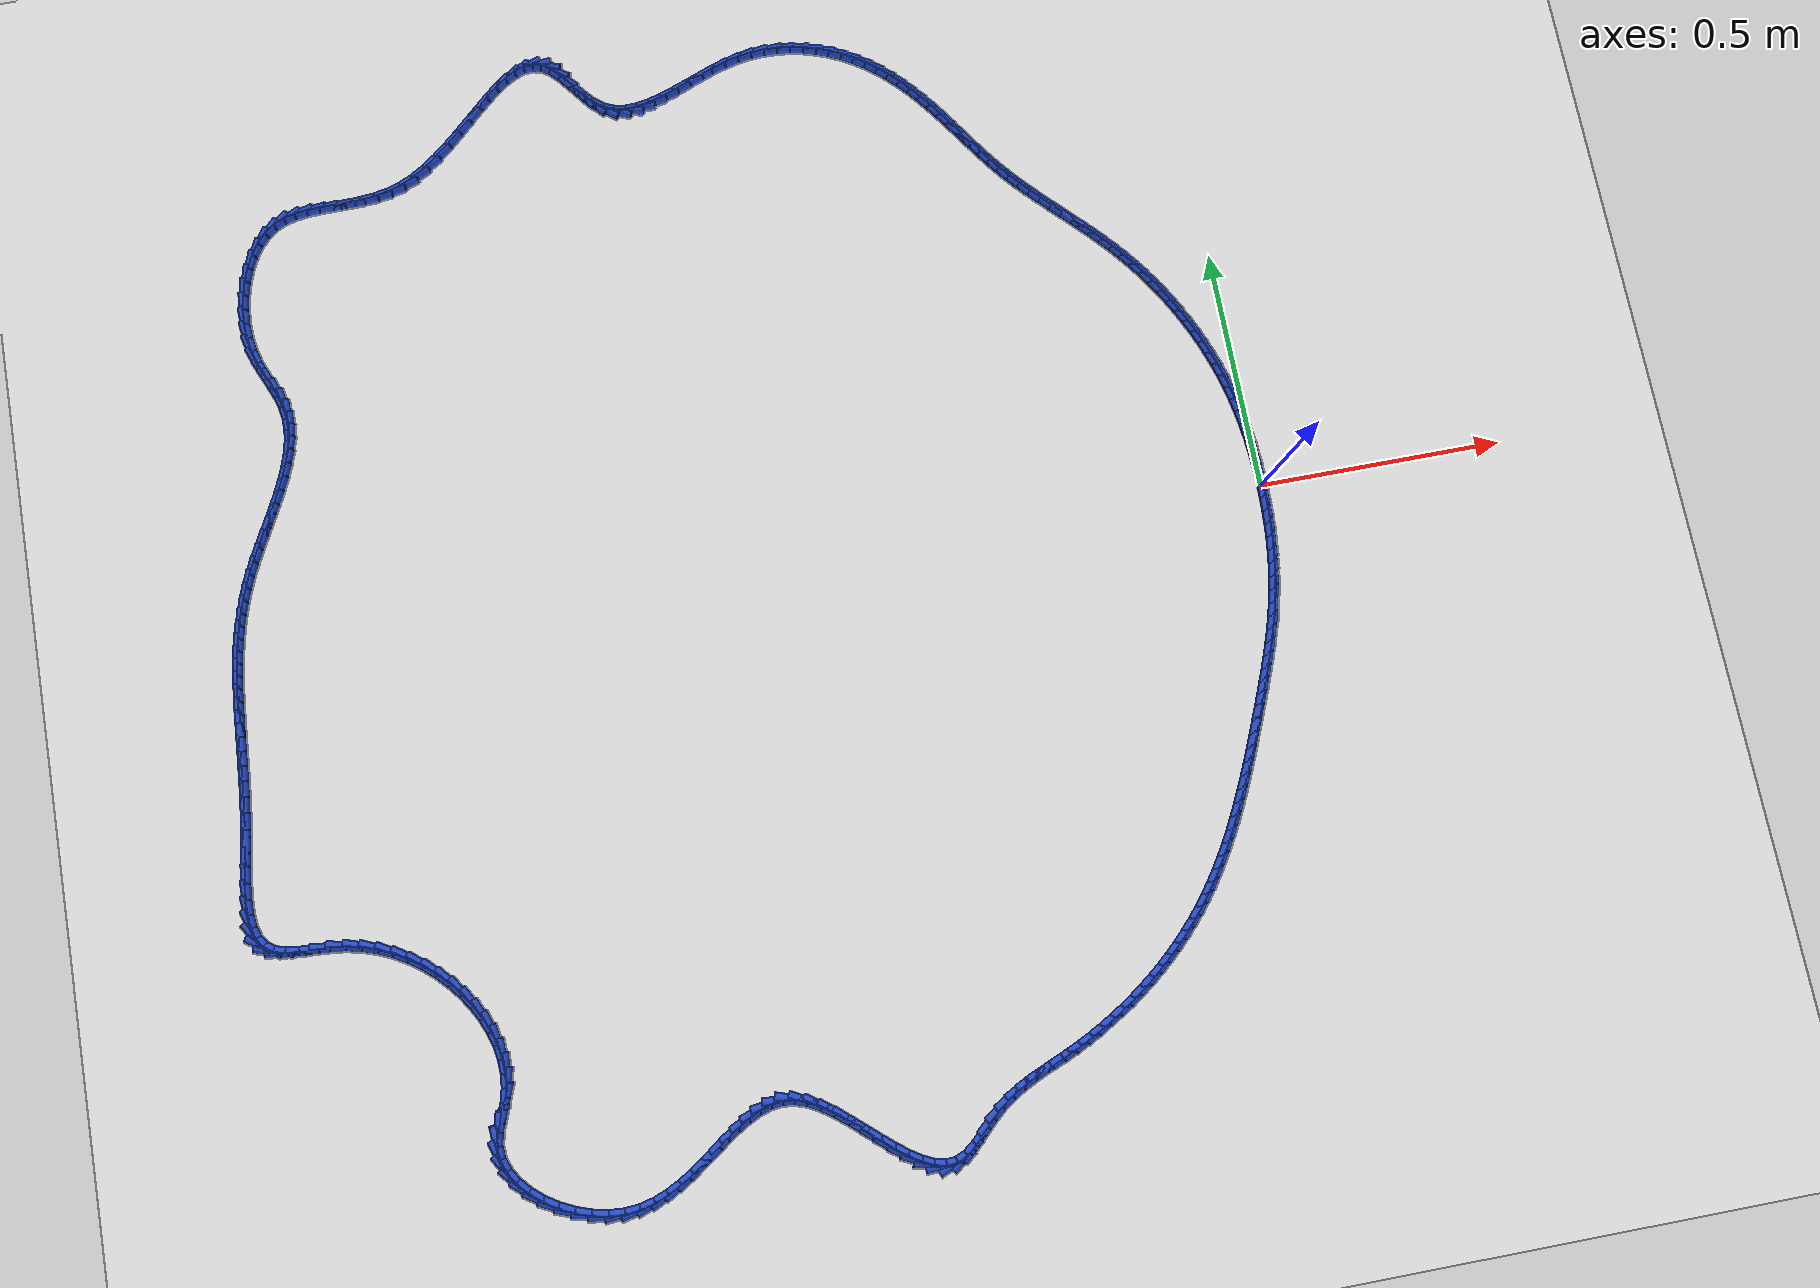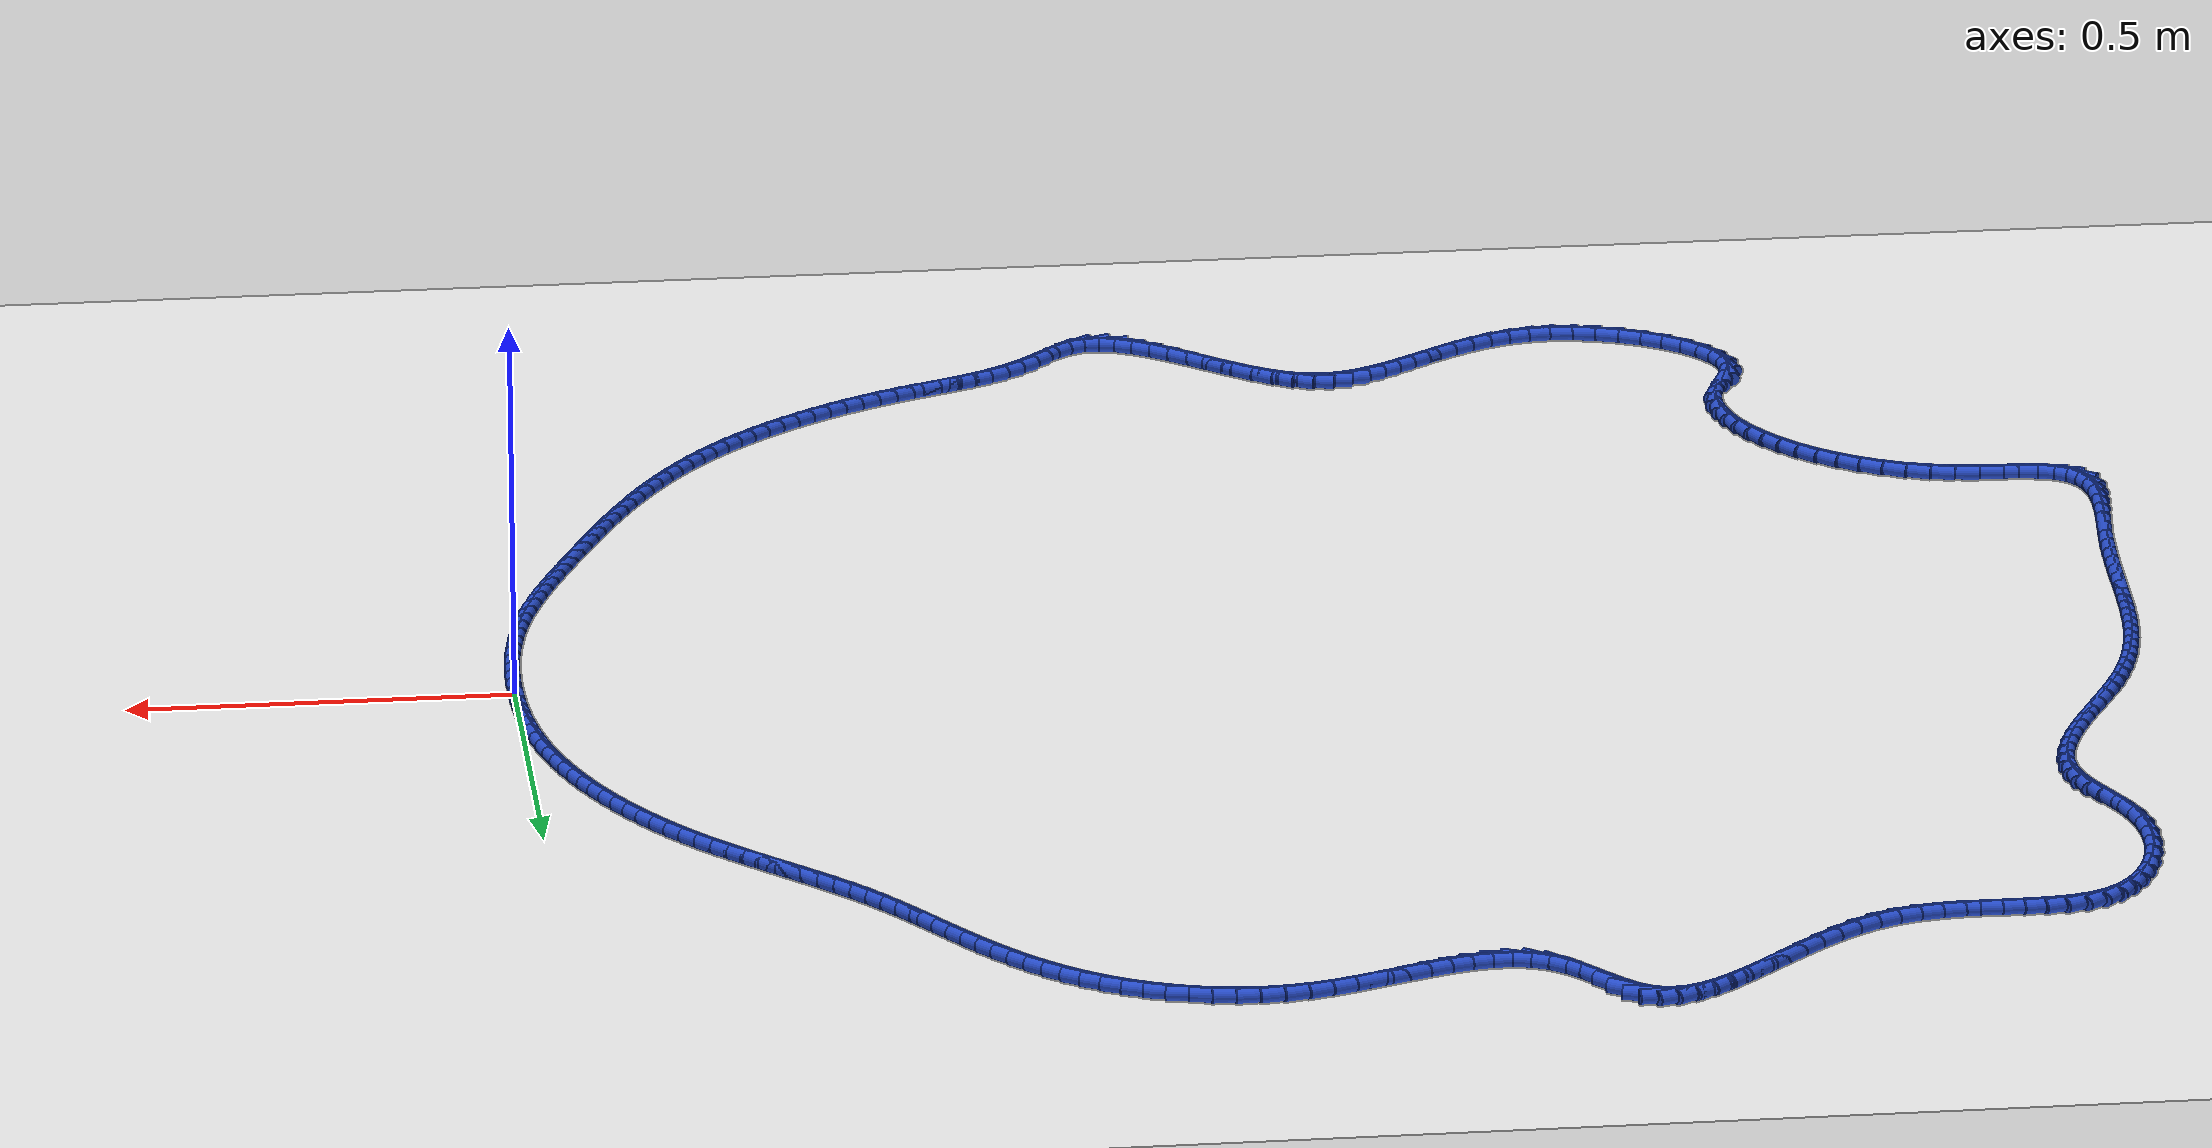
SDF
<sdf version="1.6">
 <world name="default">
  <light name="sun" type="directional">
   <pose>0 0 10 0 -0 0</pose>
   <diffuse>0.8 0.8 0.8 1</diffuse>
   <specular>0.2 0.2 0.2 1</specular>
   <attenuation>
    <range>1000</range>
    <constant>0.9</constant>
    <linear>0.01</linear>
    <quadratic>0.001</quadratic>
   </attenuation>
   <direction>-0.5 0.1 -0.9</direction>
  </light>
  <model name="ground_plane">
   <static>1</static>
   <link name="link">
    <collision name="collision">
     <geometry><plane><normal>0 0 1</normal><size>100 100</size></plane></geometry>
     <surface><friction><ode><mu>100</mu><mu2>50</mu2></ode></friction></surface>
    </collision>
    <visual name="visual">
     <cast_shadows>0</cast_shadows>
     <geometry><plane><normal>0 0 1</normal><size>100 100</size></plane></geometry>
     <material>
      <script><uri>file://media/materials/scripts/gazebo.material</uri><name>Gazebo/WhiteGlow</name></script>
     </material>
    </visual>
   </link>
  </model>
  <gravity>0 0 -9.8</gravity>
  <magnetic_field>6e-06 2.3e-05 -4.2e-05</magnetic_field>
  <atmosphere type="adiabatic"/>
  <physics name="default_physics" default="0" type="ode">
   <max_step_size>0.001</max_step_size>
   <real_time_factor>1</real_time_factor>
   <real_time_update_rate>1000</real_time_update_rate>
  </physics>
  <scene><ambient>0.4 0.4 0.4 1</ambient><background>0.7 0.7 0.7 1</background><shadows>1</shadows></scene>
  <spherical_coordinates>
   <surface_model>EARTH_WGS84</surface_model>
   <latitude_deg>0</latitude_deg>
   <longitude_deg>0</longitude_deg>
   <elevation>0</elevation>
   <heading_deg>0</heading_deg>
  </spherical_coordinates>
  <model name="line">
   <link name="link_0">
    <pose>5.204170427930421e-18 1.3877787807814457e-17 0.01 0 1.57 -1.5601567712249702</pose>
    <collision name="collision">
     <geometry><cylinder><radius>0.01</radius><length>0.08</length></cylinder></geometry>
    </collision>
    <visual name="visual">
     <material>
      <script><name>Gazebo/Blue</name><uri>file://media/materials/scripts/gazebo.material</uri></script>
     </material>
     <geometry><cylinder><radius>0.01</radius><length>0.08</length></cylinder></geometry>
    </visual>
   </link>
   <link name="link_1">
    <pose>-0.000292424796263529 0.027483644413735873 0.01 0 1.57 -1.5350626083378796</pose>
    <collision name="collision">
     <geometry><cylinder><radius>0.01</radius><length>0.08</length></cylinder></geometry>
    </collision>
    <visual name="visual">
     <material>
      <script><name>Gazebo/Blue</name><uri>file://media/materials/scripts/gazebo.material</uri></script>
     </material>
     <geometry><cylinder><radius>0.01</radius><length>0.08</length></cylinder></geometry>
    </visual>
   </link>
   <link name="link_2">
    <pose>-0.0012735811089987473 0.054929393335032016 0.01 0 1.57 -1.5085356313974962</pose>
    <collision name="collision">
     <geometry><cylinder><radius>0.01</radius><length>0.08</length></cylinder></geometry>
    </collision>
    <visual name="visual">
     <material>
      <script><name>Gazebo/Blue</name><uri>file://media/materials/scripts/gazebo.material</uri></script>
     </material>
     <geometry><cylinder><radius>0.01</radius><length>0.08</length></cylinder></geometry>
    </visual>
   </link>
   <link name="link_3">
    <pose>-0.0029808334702392625 0.08231498203880791 0.01 0 1.57 -1.48055030720396</pose>
    <collision name="collision">
     <geometry><cylinder><radius>0.01</radius><length>0.08</length></cylinder></geometry>
    </collision>
    <visual name="visual">
     <material>
      <script><name>Gazebo/Blue</name><uri>file://media/materials/scripts/gazebo.material</uri></script>
     </material>
     <geometry><cylinder><radius>0.01</radius><length>0.08</length></cylinder></geometry>
    </visual>
   </link>
   <link name="link_4">
    <pose>-0.005451546412018678 0.10961814579998304 0.01 0 1.57 -1.4510875578380813</pose>
    <collision name="collision">
     <geometry><cylinder><radius>0.01</radius><length>0.08</length></cylinder></geometry>
    </collision>
    <visual name="visual">
     <material>
      <script><name>Gazebo/Blue</name><uri>file://media/materials/scripts/gazebo.material</uri></script>
     </material>
     <geometry><cylinder><radius>0.01</radius><length>0.08</length></cylinder></geometry>
    </visual>
   </link>
   <link name="link_5">
    <pose>-0.008723084466370604 0.13681661989347693 0.01 0 1.57 -1.420136669198616</pose>
    <collision name="collision">
     <geometry><cylinder><radius>0.01</radius><length>0.08</length></cylinder></geometry>
    </collision>
    <visual name="visual">
     <material>
      <script><name>Gazebo/Blue</name><uri>file://media/materials/scripts/gazebo.material</uri></script>
     </material>
     <geometry><cylinder><radius>0.01</radius><length>0.08</length></cylinder></geometry>
    </visual>
   </link>
   <link name="link_6">
    <pose>-0.012832812165328653 0.163888139594209 0.01 0 1.57 -1.3876973370609134</pose>
    <collision name="collision">
     <geometry><cylinder><radius>0.01</radius><length>0.08</length></cylinder></geometry>
    </collision>
    <visual name="visual">
     <material>
      <script><name>Gazebo/Blue</name><uri>file://media/materials/scripts/gazebo.material</uri></script>
     </material>
     <geometry><cylinder><radius>0.01</radius><length>0.08</length></cylinder></geometry>
    </visual>
   </link>
   <link name="link_7">
    <pose>-0.017818094040926425 0.19081044017709878 0.01 0 1.57 -1.3537817924561621</pose>
    <collision name="collision">
     <geometry><cylinder><radius>0.01</radius><length>0.08</length></cylinder></geometry>
    </collision>
    <visual name="visual">
     <material>
      <script><name>Gazebo/Blue</name><uri>file://media/materials/scripts/gazebo.material</uri></script>
     </material>
     <geometry><cylinder><radius>0.01</radius><length>0.08</length></cylinder></geometry>
    </visual>
   </link>
   <link name="link_8">
    <pose>-0.023716294625197535 0.2175612569170658 0.01 0 1.57 -1.318461324378395</pose>
    <collision name="collision">
     <geometry><cylinder><radius>0.01</radius><length>0.08</length></cylinder></geometry>
    </collision>
    <visual name="visual">
     <material>
      <script><name>Gazebo/Blue</name><uri>file://media/materials/scripts/gazebo.material</uri></script>
     </material>
     <geometry><cylinder><radius>0.01</radius><length>0.08</length></cylinder></geometry>
    </visual>
   </link>
   <link name="link_9">
    <pose>-0.030563462464434803 0.24411809862682715 0.01 0 1.57 -1.2827362650244243</pose>
    <collision name="collision">
     <geometry><cylinder><radius>0.01</radius><length>0.08</length></cylinder></geometry>
    </collision>
    <visual name="visual">
     <material>
      <script><name>Gazebo/Blue</name><uri>file://media/materials/scripts/gazebo.material</uri></script>
     </material>
     <geometry><cylinder><radius>0.01</radius><length>0.08</length></cylinder></geometry>
    </visual>
   </link>
   <link name="link_10">
    <pose>-0.03836667307972044 0.27045348827853244 0.01 0 1.57 -1.2475216026046925</pose>
    <collision name="collision">
     <geometry><cylinder><radius>0.01</radius><length>0.08</length></cylinder></geometry>
    </collision>
    <visual name="visual">
     <material>
      <script><name>Gazebo/Blue</name><uri>file://media/materials/scripts/gazebo.material</uri></script>
     </material>
     <geometry><cylinder><radius>0.01</radius><length>0.08</length></cylinder></geometry>
    </visual>
   </link>
   <link name="link_11">
    <pose>-0.04710473046950239 0.29653508372225795 0.01 0 1.57 -1.212797011041639</pose>
    <collision name="collision">
     <geometry><cylinder><radius>0.01</radius><length>0.08</length></cylinder></geometry>
    </collision>
    <visual name="visual">
     <material>
      <script><name>Gazebo/Blue</name><uri>file://media/materials/scripts/gazebo.material</uri></script>
     </material>
     <geometry><cylinder><radius>0.01</radius><length>0.08</length></cylinder></geometry>
    </visual>
   </link>
   <link name="link_12">
    <pose>-0.056755262973425584 0.3223303404941242 0.01 0 1.57 -1.1785001450796435</pose>
    <collision name="collision">
     <geometry><cylinder><radius>0.01</radius><length>0.08</length></cylinder></geometry>
    </collision>
    <visual name="visual">
     <material>
      <script><name>Gazebo/Blue</name><uri>file://media/materials/scripts/gazebo.material</uri></script>
     </material>
     <geometry><cylinder><radius>0.01</radius><length>0.08</length></cylinder></geometry>
    </visual>
   </link>
   <link name="link_13">
    <pose>-0.06729589893113488 0.3478067141302512 0.01 0 1.57 -1.1445667894212852</pose>
    <collision name="collision">
     <geometry><cylinder><radius>0.01</radius><length>0.08</length></cylinder></geometry>
    </collision>
    <visual name="visual">
     <material>
      <script><name>Gazebo/Blue</name><uri>file://media/materials/scripts/gazebo.material</uri></script>
     </material>
     <geometry><cylinder><radius>0.01</radius><length>0.08</length></cylinder></geometry>
    </visual>
   </link>
   <link name="link_14">
    <pose>-0.07870426668227531 0.3729316601667595 0.01 0 1.57 -1.1109312485228011</pose>
    <collision name="collision">
     <geometry><cylinder><radius>0.01</radius><length>0.08</length></cylinder></geometry>
    </collision>
    <visual name="visual">
     <material>
      <script><name>Gazebo/Blue</name><uri>file://media/materials/scripts/gazebo.material</uri></script>
     </material>
     <geometry><cylinder><radius>0.01</radius><length>0.08</length></cylinder></geometry>
    </visual>
   </link>
   <link name="link_15">
    <pose>-0.09095799456649167 0.3976726341397691 0.01 0 1.57 -1.0775266589312067</pose>
    <collision name="collision">
     <geometry><cylinder><radius>0.01</radius><length>0.08</length></cylinder></geometry>
    </collision>
    <visual name="visual">
     <material>
      <script><name>Gazebo/Blue</name><uri>file://media/materials/scripts/gazebo.material</uri></script>
     </material>
     <geometry><cylinder><radius>0.01</radius><length>0.08</length></cylinder></geometry>
    </visual>
   </link>
   <link name="link_16">
    <pose>-0.10403471092342897 0.42199709158540066 0.01 0 1.57 -1.044285237611704</pose>
    <collision name="collision">
     <geometry><cylinder><radius>0.01</radius><length>0.08</length></cylinder></geometry>
    </collision>
    <visual name="visual">
     <material>
      <script><name>Gazebo/Blue</name><uri>file://media/materials/scripts/gazebo.material</uri></script>
     </material>
     <geometry><cylinder><radius>0.01</radius><length>0.08</length></cylinder></geometry>
    </visual>
   </link>
   <link name="link_17">
    <pose>-0.11791204409273214 0.4458724880397742 0.01 0 1.57 -1.0111384799611873</pose>
    <collision name="collision">
     <geometry><cylinder><radius>0.01</radius><length>0.08</length></cylinder></geometry>
    </collision>
    <visual name="visual">
     <material>
      <script><name>Gazebo/Blue</name><uri>file://media/materials/scripts/gazebo.material</uri></script>
     </material>
     <geometry><cylinder><radius>0.01</radius><length>0.08</length></cylinder></geometry>
    </visual>
   </link>
   <link name="link_18">
    <pose>-0.13256762241404596 0.46926627903900986 0.01 0 1.57 -0.9780173212782878</pose>
    <collision name="collision">
     <geometry><cylinder><radius>0.01</radius><length>0.08</length></cylinder></geometry>
    </collision>
    <visual name="visual">
     <material>
      <script><name>Gazebo/Blue</name><uri>file://media/materials/scripts/gazebo.material</uri></script>
     </material>
     <geometry><cylinder><radius>0.01</radius><length>0.08</length></cylinder></geometry>
    </visual>
   </link>
   <link name="link_19">
    <pose>-0.1479790742270155 0.4921459201192282 0.01 0 1.57 -0.9448522754947057</pose>
    <collision name="collision">
     <geometry><cylinder><radius>0.01</radius><length>0.08</length></cylinder></geometry>
    </collision>
    <visual name="visual">
     <material>
      <script><name>Gazebo/Blue</name><uri>file://media/materials/scripts/gazebo.material</uri></script>
     </material>
     <geometry><cylinder><radius>0.01</radius><length>0.08</length></cylinder></geometry>
    </visual>
   </link>
   <link name="link_20">
    <pose>-0.16412402787128563 0.5144788668165494 0.01 0 1.57 -0.9115735650611517</pose>
    <collision name="collision">
     <geometry><cylinder><radius>0.01</radius><length>0.08</length></cylinder></geometry>
    </collision>
    <visual name="visual">
     <material>
      <script><name>Gazebo/Blue</name><uri>file://media/materials/scripts/gazebo.material</uri></script>
     </material>
     <geometry><cylinder><radius>0.01</radius><length>0.08</length></cylinder></geometry>
    </visual>
   </link>
   <link name="link_21">
    <pose>-0.1809801116865013 0.5362325746670938 0.01 0 1.57 -0.8784412272285269</pose>
    <collision name="collision">
     <geometry><cylinder><radius>0.01</radius><length>0.08</length></cylinder></geometry>
    </collision>
    <visual name="visual">
     <material>
      <script><name>Gazebo/Blue</name><uri>file://media/materials/scripts/gazebo.material</uri></script>
     </material>
     <geometry><cylinder><radius>0.01</radius><length>0.08</length></cylinder></geometry>
    </visual>
   </link>
   <link name="link_22">
    <pose>-0.1985193891395126 0.5573819903523333 0.01 0 1.57 -0.8491160964049878</pose>
    <collision name="collision">
     <geometry><cylinder><radius>0.01</radius><length>0.08</length></cylinder></geometry>
    </collision>
    <visual name="visual">
     <material>
      <script><name>Gazebo/Blue</name><uri>file://media/materials/scripts/gazebo.material</uri></script>
     </material>
     <geometry><cylinder><radius>0.01</radius><length>0.08</length></cylinder></geometry>
    </visual>
   </link>
   <link name="link_23">
    <pose>-0.21665169526553926 0.577985829265717 0.01 0 1.57 -0.8259614706746266</pose>
    <collision name="collision">
     <geometry><cylinder><radius>0.01</radius><length>0.08</length></cylinder></geometry>
    </collision>
    <visual name="visual">
     <material>
      <script><name>Gazebo/Blue</name><uri>file://media/materials/scripts/gazebo.material</uri></script>
     </material>
     <geometry><cylinder><radius>0.01</radius><length>0.08</length></cylinder></geometry>
    </visual>
   </link>
   <link name="link_24">
    <pose>-0.23524785722446198 0.598155317194875 0.01 0 1.57 -0.8090396696403415</pose>
    <collision name="collision">
     <geometry><cylinder><radius>0.01</radius><length>0.08</length></cylinder></geometry>
    </collision>
    <visual name="visual">
     <material>
      <script><name>Gazebo/Blue</name><uri>file://media/materials/scripts/gazebo.material</uri></script>
     </material>
     <geometry><cylinder><radius>0.01</radius><length>0.08</length></cylinder></geometry>
    </visual>
   </link>
   <link name="link_25">
    <pose>-0.2541781013746335 0.6180024886955326 0.01 0 1.57 -0.7983538027062772</pose>
    <collision name="collision">
     <geometry><cylinder><radius>0.01</radius><length>0.08</length></cylinder></geometry>
    </collision>
    <visual name="visual">
     <material>
      <script><name>Gazebo/Blue</name><uri>file://media/materials/scripts/gazebo.material</uri></script>
     </material>
     <geometry><cylinder><radius>0.01</radius><length>0.08</length></cylinder></geometry>
    </visual>
   </link>
   <link name="link_26">
    <pose>-0.2733126540744067 0.6376393783234156 0.01 0 1.57 -0.7939030940804408</pose>
    <collision name="collision">
     <geometry><cylinder><radius>0.01</radius><length>0.08</length></cylinder></geometry>
    </collision>
    <visual name="visual">
     <material>
      <script><name>Gazebo/Blue</name><uri>file://media/materials/scripts/gazebo.material</uri></script>
     </material>
     <geometry><cylinder><radius>0.01</radius><length>0.08</length></cylinder></geometry>
    </visual>
   </link>
   <link name="link_27">
    <pose>-0.29252174168213446 0.6571780206342487 0.01 0 1.57 -0.7956953710884858</pose>
    <collision name="collision">
     <geometry><cylinder><radius>0.01</radius><length>0.08</length></cylinder></geometry>
    </collision>
    <visual name="visual">
     <material>
      <script><name>Gazebo/Blue</name><uri>file://media/materials/scripts/gazebo.material</uri></script>
     </material>
     <geometry><cylinder><radius>0.01</radius><length>0.08</length></cylinder></geometry>
    </visual>
   </link>
   <link name="link_28">
    <pose>-0.3116755905561697 0.6767304501837579 0.01 0 1.57 -0.8037523324053812</pose>
    <collision name="collision">
     <geometry><cylinder><radius>0.01</radius><length>0.08</length></cylinder></geometry>
    </collision>
    <visual name="visual">
     <material>
      <script><name>Gazebo/Blue</name><uri>file://media/materials/scripts/gazebo.material</uri></script>
     </material>
     <geometry><cylinder><radius>0.01</radius><length>0.08</length></cylinder></geometry>
    </visual>
   </link>
   <link name="link_29">
    <pose>-0.33064442705486513 0.6964087015276683 0.01 0 1.57 -0.8181075725865407</pose>
    <collision name="collision">
     <geometry><cylinder><radius>0.01</radius><length>0.08</length></cylinder></geometry>
    </collision>
    <visual name="visual">
     <material>
      <script><name>Gazebo/Blue</name><uri>file://media/materials/scripts/gazebo.material</uri></script>
     </material>
     <geometry><cylinder><radius>0.01</radius><length>0.08</length></cylinder></geometry>
    </visual>
   </link>
   <link name="link_30">
    <pose>-0.34929847753657367 0.7163248092217055 0.01 0 1.57 -0.8387971651323322</pose>
    <collision name="collision">
     <geometry><cylinder><radius>0.01</radius><length>0.08</length></cylinder></geometry>
    </collision>
    <visual name="visual">
     <material>
      <script><name>Gazebo/Blue</name><uri>file://media/materials/scripts/gazebo.material</uri></script>
     </material>
     <geometry><cylinder><radius>0.01</radius><length>0.08</length></cylinder></geometry>
    </visual>
   </link>
   <link name="link_31">
    <pose>-0.3675079683596481 0.7365908078215946 0.01 0 1.57 -0.8658424899538193</pose>
    <collision name="collision">
     <geometry><cylinder><radius>0.01</radius><length>0.08</length></cylinder></geometry>
    </collision>
    <visual name="visual">
     <material>
      <script><name>Gazebo/Blue</name><uri>file://media/materials/scripts/gazebo.material</uri></script>
     </material>
     <geometry><cylinder><radius>0.01</radius><length>0.08</length></cylinder></geometry>
    </visual>
   </link>
   <link name="link_32">
    <pose>-0.3851431258824413 0.7573187318830612 0.01 0 1.57 -0.8989108063107654</pose>
    <collision name="collision">
     <geometry><cylinder><radius>0.01</radius><length>0.08</length></cylinder></geometry>
    </collision>
    <visual name="visual">
     <material>
      <script><name>Gazebo/Blue</name><uri>file://media/materials/scripts/gazebo.material</uri></script>
     </material>
     <geometry><cylinder><radius>0.01</radius><length>0.08</length></cylinder></geometry>
    </visual>
   </link>
   <link name="link_33">
    <pose>-0.40208083167461295 0.7786152419017476 0.01 0 1.57 -0.9306602874152675</pose>
    <collision name="collision">
     <geometry><cylinder><radius>0.01</radius><length>0.08</length></cylinder></geometry>
    </collision>
    <visual name="visual">
     <material>
      <script><name>Gazebo/Blue</name><uri>file://media/materials/scripts/gazebo.material</uri></script>
     </material>
     <geometry><cylinder><radius>0.01</radius><length>0.08</length></cylinder></geometry>
    </visual>
   </link>
   <link name="link_34">
    <pose>-0.4183518628415559 0.8004627282611356 0.01 0 1.57 -0.9537615742624455</pose>
    <collision name="collision">
     <geometry><cylinder><radius>0.01</radius><length>0.08</length></cylinder></geometry>
    </collision>
    <visual name="visual">
     <material>
      <script><name>Gazebo/Blue</name><uri>file://media/materials/scripts/gazebo.material</uri></script>
     </material>
     <geometry><cylinder><radius>0.01</radius><length>0.08</length></cylinder></geometry>
    </visual>
   </link>
   <link name="link_35">
    <pose>-0.43414135213555904 0.8227189396943771 0.01 0 1.57 -0.9679293875613233</pose>
    <collision name="collision">
     <geometry><cylinder><radius>0.01</radius><length>0.08</length></cylinder></geometry>
    </collision>
    <visual name="visual">
     <material>
      <script><name>Gazebo/Blue</name><uri>file://media/materials/scripts/gazebo.material</uri></script>
     </material>
     <geometry><cylinder><radius>0.01</radius><length>0.08</length></cylinder></geometry>
    </visual>
   </link>
   <link name="link_36">
    <pose>-0.4496411795427079 0.8452361765666986 0.01 0 1.57 -0.9732190251502583</pose>
    <collision name="collision">
     <geometry><cylinder><radius>0.01</radius><length>0.08</length></cylinder></geometry>
    </collision>
    <visual name="visual">
     <material>
      <script><name>Gazebo/Blue</name><uri>file://media/materials/scripts/gazebo.material</uri></script>
     </material>
     <geometry><cylinder><radius>0.01</radius><length>0.08</length></cylinder></geometry>
    </visual>
   </link>
   <link name="link_37">
    <pose>-0.46504322504908735 0.8678667392433268 0.01 0 1.57 -0.9696739872765708</pose>
    <collision name="collision">
     <geometry><cylinder><radius>0.01</radius><length>0.08</length></cylinder></geometry>
    </collision>
    <visual name="visual">
     <material>
      <script><name>Gazebo/Blue</name><uri>file://media/materials/scripts/gazebo.material</uri></script>
     </material>
     <geometry><cylinder><radius>0.01</radius><length>0.08</length></cylinder></geometry>
    </visual>
   </link>
   <link name="link_38">
    <pose>-0.4805393686407831 0.8904629280894885 0.01 0 1.57 -0.9573137500110067</pose>
    <collision name="collision">
     <geometry><cylinder><radius>0.01</radius><length>0.08</length></cylinder></geometry>
    </collision>
    <visual name="visual">
     <material>
      <script><name>Gazebo/Blue</name><uri>file://media/materials/scripts/gazebo.material</uri></script>
     </material>
     <geometry><cylinder><radius>0.01</radius><length>0.08</length></cylinder></geometry>
    </visual>
   </link>
   <link name="link_39">
    <pose>-0.4963214903038802 0.9128770434704099 0.01 0 1.57 -0.9361422142391677</pose>
    <collision name="collision">
     <geometry><cylinder><radius>0.01</radius><length>0.08</length></cylinder></geometry>
    </collision>
    <visual name="visual">
     <material>
      <script><name>Gazebo/Blue</name><uri>file://media/materials/scripts/gazebo.material</uri></script>
     </material>
     <geometry><cylinder><radius>0.01</radius><length>0.08</length></cylinder></geometry>
    </visual>
   </link>
   <link name="link_40">
    <pose>-0.5125814700244635 0.9349613857513178 0.01 0 1.57 -0.9061978779624982</pose>
    <collision name="collision">
     <geometry><cylinder><radius>0.01</radius><length>0.08</length></cylinder></geometry>
    </collision>
    <visual name="visual">
     <material>
      <script><name>Gazebo/Blue</name><uri>file://media/materials/scripts/gazebo.material</uri></script>
     </material>
     <geometry><cylinder><radius>0.01</radius><length>0.08</length></cylinder></geometry>
    </visual>
   </link>
   <link name="link_41">
    <pose>-0.5295102947037077 0.9565680643680382 0.01 0 1.57 -0.8686071542196805</pose>
    <collision name="collision">
     <geometry><cylinder><radius>0.01</radius><length>0.08</length></cylinder></geometry>
    </collision>
    <visual name="visual">
     <material>
      <script><name>Gazebo/Blue</name><uri>file://media/materials/scripts/gazebo.material</uri></script>
     </material>
     <geometry><cylinder><radius>0.01</radius><length>0.08</length></cylinder></geometry>
    </visual>
   </link>
   <link name="link_42">
    <pose>-0.5472527596798153 0.9775393136288042 0.01 0 1.57 -0.8248225254175654</pose>
    <collision name="collision">
     <geometry><cylinder><radius>0.01</radius><length>0.08</length></cylinder></geometry>
    </collision>
    <visual name="visual">
     <material>
      <script><name>Gazebo/Blue</name><uri>file://media/materials/scripts/gazebo.material</uri></script>
     </material>
     <geometry><cylinder><radius>0.01</radius><length>0.08</length></cylinder></geometry>
    </visual>
   </link>
   <link name="link_43">
    <pose>-0.5658860189990271 0.9977029070540846 0.01 0 1.57 -0.7747414183541284</pose>
    <collision name="collision">
     <geometry><cylinder><radius>0.01</radius><length>0.08</length></cylinder></geometry>
    </collision>
    <visual name="visual">
     <material>
      <script><name>Gazebo/Blue</name><uri>file://media/materials/scripts/gazebo.material</uri></script>
     </material>
     <geometry><cylinder><radius>0.01</radius><length>0.08</length></cylinder></geometry>
    </visual>
   </link>
   <link name="link_44">
    <pose>-0.5854818470650754 1.016885468069986 0.01 0 1.57 -0.7181914086654505</pose>
    <collision name="collision">
     <geometry><cylinder><radius>0.01</radius><length>0.08</length></cylinder></geometry>
    </collision>
    <visual name="visual">
     <material>
      <script><name>Gazebo/Blue</name><uri>file://media/materials/scripts/gazebo.material</uri></script>
     </material>
     <geometry><cylinder><radius>0.01</radius><length>0.08</length></cylinder></geometry>
    </visual>
   </link>
   <link name="link_45">
    <pose>-0.6061120182816933 1.0349136201026141 0.01 0 1.57 -0.6551214767461419</pose>
    <collision name="collision">
     <geometry><cylinder><radius>0.01</radius><length>0.08</length></cylinder></geometry>
    </collision>
    <visual name="visual">
     <material>
      <script><name>Gazebo/Blue</name><uri>file://media/materials/scripts/gazebo.material</uri></script>
     </material>
     <geometry><cylinder><radius>0.01</radius><length>0.08</length></cylinder></geometry>
    </visual>
   </link>
   <link name="link_46">
    <pose>-0.6278483070526133 1.051613986578076 0.01 0 1.57 -0.5864121940429476</pose>
    <collision name="collision">
     <geometry><cylinder><radius>0.01</radius><length>0.08</length></cylinder></geometry>
    </collision>
    <visual name="visual">
     <material>
      <script><name>Gazebo/Blue</name><uri>file://media/materials/scripts/gazebo.material</uri></script>
     </material>
     <geometry><cylinder><radius>0.01</radius><length>0.08</length></cylinder></geometry>
    </visual>
   </link>
   <link name="link_47">
    <pose>-0.6507348701033847 1.0668191745765627 0.01 0 1.57 -0.5150181969271446</pose>
    <collision name="collision">
     <geometry><cylinder><radius>0.01</radius><length>0.08</length></cylinder></geometry>
    </collision>
    <visual name="visual">
     <material>
      <script><name>Gazebo/Blue</name><uri>file://media/materials/scripts/gazebo.material</uri></script>
     </material>
     <geometry><cylinder><radius>0.01</radius><length>0.08</length></cylinder></geometry>
    </visual>
   </link>
   <link name="link_48">
    <pose>-0.6747054690454833 1.0803857094153761 0.01 0 1.57 -0.4412885654606538</pose>
    <collision name="collision">
     <geometry><cylinder><radius>0.01</radius><length>0.08</length></cylinder></geometry>
    </collision>
    <visual name="visual">
     <material>
      <script><name>Gazebo/Blue</name><uri>file://media/materials/scripts/gazebo.material</uri></script>
     </material>
     <geometry><cylinder><radius>0.01</radius><length>0.08</length></cylinder></geometry>
    </visual>
   </link>
   <link name="link_49">
    <pose>-0.6996662855985998 1.0921760918790904 0.01 0 1.57 -0.3648690006106544</pose>
    <collision name="collision">
     <geometry><cylinder><radius>0.01</radius><length>0.08</length></cylinder></geometry>
    </collision>
    <visual name="visual">
     <material>
      <script><name>Gazebo/Blue</name><uri>file://media/materials/scripts/gazebo.material</uri></script>
     </material>
     <geometry><cylinder><radius>0.01</radius><length>0.08</length></cylinder></geometry>
    </visual>
   </link>
   <link name="link_50">
    <pose>-0.7255235014824252 1.1020528227522801 0.01 0 1.57 -0.28551498090484334</pose>
    <collision name="collision">
     <geometry><cylinder><radius>0.01</radius><length>0.08</length></cylinder></geometry>
    </collision>
    <visual name="visual">
     <material>
      <script><name>Gazebo/Blue</name><uri>file://media/materials/scripts/gazebo.material</uri></script>
     </material>
     <geometry><cylinder><radius>0.01</radius><length>0.08</length></cylinder></geometry>
    </visual>
   </link>
   <link name="link_51">
    <pose>-0.7521832984166503 1.10987840281952 0.01 0 1.57 -0.20312326307342912</pose>
    <collision name="collision">
     <geometry><cylinder><radius>0.01</radius><length>0.08</length></cylinder></geometry>
    </collision>
    <visual name="visual">
     <material>
      <script><name>Gazebo/Blue</name><uri>file://media/materials/scripts/gazebo.material</uri></script>
     </material>
     <geometry><cylinder><radius>0.01</radius><length>0.08</length></cylinder></geometry>
    </visual>
   </link>
   <link name="link_52">
    <pose>-0.7795518581209665 1.1155153328653846 0.01 0 1.57 -0.11776443262450144</pose>
    <collision name="collision">
     <geometry><cylinder><radius>0.01</radius><length>0.08</length></cylinder></geometry>
    </collision>
    <visual name="visual">
     <material>
      <script><name>Gazebo/Blue</name><uri>file://media/materials/scripts/gazebo.material</uri></script>
     </material>
     <geometry><cylinder><radius>0.01</radius><length>0.08</length></cylinder></geometry>
    </visual>
   </link>
   <link name="link_53">
    <pose>-0.8075353623150642 1.1188261136744482 0.01 0 1.57 -0.029710368943580347</pose>
    <collision name="collision">
     <geometry><cylinder><radius>0.01</radius><length>0.08</length></cylinder></geometry>
    </collision>
    <visual name="visual">
     <material>
      <script><name>Gazebo/Blue</name><uri>file://media/materials/scripts/gazebo.material</uri></script>
     </material>
     <geometry><cylinder><radius>0.01</radius><length>0.08</length></cylinder></geometry>
    </visual>
   </link>
   <link name="link_54">
    <pose>-0.8360399927186347 1.1196732460312857 0.01 0 1.57 0.06055145975937655</pose>
    <collision name="collision">
     <geometry><cylinder><radius>0.01</radius><length>0.08</length></cylinder></geometry>
    </collision>
    <visual name="visual">
     <material>
      <script><name>Gazebo/Blue</name><uri>file://media/materials/scripts/gazebo.material</uri></script>
     </material>
     <geometry><cylinder><radius>0.01</radius><length>0.08</length></cylinder></geometry>
    </visual>
   </link>
   <link name="link_55">
    <pose>-0.8649719310513689 1.117919230720471 0.01 0 1.57 0.15232514810783981</pose>
    <collision name="collision">
     <geometry><cylinder><radius>0.01</radius><length>0.08</length></cylinder></geometry>
    </collision>
    <visual name="visual">
     <material>
      <script><name>Gazebo/Blue</name><uri>file://media/materials/scripts/gazebo.material</uri></script>
     </material>
     <geometry><cylinder><radius>0.01</radius><length>0.08</length></cylinder></geometry>
    </visual>
   </link>
   <link name="link_56">
    <pose>-0.8942373590329572 1.1134265685265787 0.01 0 1.57 0.24121271263919725</pose>
    <collision name="collision">
     <geometry><cylinder><radius>0.01</radius><length>0.08</length></cylinder></geometry>
    </collision>
    <visual name="visual">
     <material>
      <script><name>Gazebo/Blue</name><uri>file://media/materials/scripts/gazebo.material</uri></script>
     </material>
     <geometry><cylinder><radius>0.01</radius><length>0.08</length></cylinder></geometry>
    </visual>
   </link>
   <link name="link_57">
    <pose>-0.9237328816446243 1.106170598514795 0.01 0 1.57 0.30754703550486334</pose>
    <collision name="collision">
     <geometry><cylinder><radius>0.01</radius><length>0.08</length></cylinder></geometry>
    </collision>
    <visual name="visual">
     <material>
      <script><name>Gazebo/Blue</name><uri>file://media/materials/scripts/gazebo.material</uri></script>
     </material>
     <geometry><cylinder><radius>0.01</radius><length>0.08</length></cylinder></geometry>
    </visual>
   </link>
   <link name="link_58">
    <pose>-0.9532997016489073 1.0967794384724598 0.01 0 1.57 0.3473164274571994</pose>
    <collision name="collision">
     <geometry><cylinder><radius>0.01</radius><length>0.08</length></cylinder></geometry>
    </collision>
    <visual name="visual">
     <material>
      <script><name>Gazebo/Blue</name><uri>file://media/materials/scripts/gazebo.material</uri></script>
     </material>
     <geometry><cylinder><radius>0.01</radius><length>0.08</length></cylinder></geometry>
    </visual>
   </link>
   <link name="link_59">
    <pose>-0.9827591450152 1.0861154052485402 0.01 0 1.57 0.36279974582739744</pose>
    <collision name="collision">
     <geometry><cylinder><radius>0.01</radius><length>0.08</length></cylinder></geometry>
    </collision>
    <visual name="visual">
     <material>
      <script><name>Gazebo/Blue</name><uri>file://media/materials/scripts/gazebo.material</uri></script>
     </material>
     <geometry><cylinder><radius>0.01</radius><length>0.08</length></cylinder></geometry>
    </visual>
   </link>
   <link name="link_60">
    <pose>-1.0119325120552334 1.0750411180043788 0.01 0 1.57 0.3543720580149569</pose>
    <collision name="collision">
     <geometry><cylinder><radius>0.01</radius><length>0.08</length></cylinder></geometry>
    </collision>
    <visual name="visual">
     <material>
      <script><name>Gazebo/Blue</name><uri>file://media/materials/scripts/gazebo.material</uri></script>
     </material>
     <geometry><cylinder><radius>0.01</radius><length>0.08</length></cylinder></geometry>
    </visual>
   </link>
   <link name="link_61">
    <pose>-1.0406411030807383 1.0644191959013207 0.01 0 1.57 0.32020725726535043</pose>
    <collision name="collision">
     <geometry><cylinder><radius>0.01</radius><length>0.08</length></cylinder></geometry>
    </collision>
    <visual name="visual">
     <material>
      <script><name>Gazebo/Blue</name><uri>file://media/materials/scripts/gazebo.material</uri></script>
     </material>
     <geometry><cylinder><radius>0.01</radius><length>0.08</length></cylinder></geometry>
    </visual>
   </link>
   <link name="link_62">
    <pose>-1.068706218403446 1.0551122581007095 0.01 0 1.57 0.2559548408038045</pose>
    <collision name="collision">
     <geometry><cylinder><radius>0.01</radius><length>0.08</length></cylinder></geometry>
    </collision>
    <visual name="visual">
     <material>
      <script><name>Gazebo/Blue</name><uri>file://media/materials/scripts/gazebo.material</uri></script>
     </material>
     <geometry><cylinder><radius>0.01</radius><length>0.08</length></cylinder></geometry>
    </visual>
   </link>
   <link name="link_63">
    <pose>-1.0959491583350862 1.0479829237638891 0.01 0 1.57 0.15457968431410574</pose>
    <collision name="collision">
     <geometry><cylinder><radius>0.01</radius><length>0.08</length></cylinder></geometry>
    </collision>
    <visual name="visual">
     <material>
      <script><name>Gazebo/Blue</name><uri>file://media/materials/scripts/gazebo.material</uri></script>
     </material>
     <geometry><cylinder><radius>0.01</radius><length>0.08</length></cylinder></geometry>
    </visual>
   </link>
   <link name="link_64">
    <pose>-1.1221912231873916 1.043893812052204 0.01 0 1.57 0.007432082565260044</pose>
    <collision name="collision">
     <geometry><cylinder><radius>0.01</radius><length>0.08</length></cylinder></geometry>
    </collision>
    <visual name="visual">
     <material>
      <script><name>Gazebo/Blue</name><uri>file://media/materials/scripts/gazebo.material</uri></script>
     </material>
     <geometry><cylinder><radius>0.01</radius><length>0.08</length></cylinder></geometry>
    </visual>
   </link>
   <link name="link_65">
    <pose>-1.1472537132720921 1.0437075421269983 0.01 0 1.57 -0.1908297829703688</pose>
    <collision name="collision">
     <geometry><cylinder><radius>0.01</radius><length>0.08</length></cylinder></geometry>
    </collision>
    <visual name="visual">
     <material>
      <script><name>Gazebo/Blue</name><uri>file://media/materials/scripts/gazebo.material</uri></script>
     </material>
     <geometry><cylinder><radius>0.01</radius><length>0.08</length></cylinder></geometry>
    </visual>
   </link>
   <link name="link_66">
    <pose>-1.1709579289009193 1.048286733149616 0.01 0 1.57 -0.4315236645023768</pose>
    <collision name="collision">
     <geometry><cylinder><radius>0.01</radius><length>0.08</length></cylinder></geometry>
    </collision>
    <visual name="visual">
     <material>
      <script><name>Gazebo/Blue</name><uri>file://media/materials/scripts/gazebo.material</uri></script>
     </material>
     <geometry><cylinder><radius>0.01</radius><length>0.08</length></cylinder></geometry>
    </visual>
   </link>
   <link name="link_67">
    <pose>-1.193125170385603 1.0584940042814004 0.01 0 1.57 -0.6776256047833608</pose>
    <collision name="collision">
     <geometry><cylinder><radius>0.01</radius><length>0.08</length></cylinder></geometry>
    </collision>
    <visual name="visual">
     <material>
      <script><name>Gazebo/Blue</name><uri>file://media/materials/scripts/gazebo.material</uri></script>
     </material>
     <geometry><cylinder><radius>0.01</radius><length>0.08</length></cylinder></geometry>
    </visual>
   </link>
   <link name="link_68">
    <pose>-1.213614786763767 1.0749828550991414 0.01 0 1.57 -0.8388271453179427</pose>
    <collision name="collision">
     <geometry><cylinder><radius>0.01</radius><length>0.08</length></cylinder></geometry>
    </collision>
    <visual name="visual">
     <material>
      <script><name>Gazebo/Blue</name><uri>file://media/materials/scripts/gazebo.material</uri></script>
     </material>
     <geometry><cylinder><radius>0.01</radius><length>0.08</length></cylinder></geometry>
    </visual>
   </link>
   <link name="link_69">
    <pose>-1.2326859800498944 1.0962091534207812 0.01 0 1.57 -0.9049081927433106</pose>
    <collision name="collision">
     <geometry><cylinder><radius>0.01</radius><length>0.08</length></cylinder></geometry>
    </collision>
    <visual name="visual">
     <material>
      <script><name>Gazebo/Blue</name><uri>file://media/materials/scripts/gazebo.material</uri></script>
     </material>
     <geometry><cylinder><radius>0.01</radius><length>0.08</length></cylinder></geometry>
    </visual>
   </link>
   <link name="link_70">
    <pose>-1.2508370928147665 1.1193144267647905 0.01 0 1.57 -0.8947844522712578</pose>
    <collision name="collision">
     <geometry><cylinder><radius>0.01</radius><length>0.08</length></cylinder></geometry>
    </collision>
    <visual name="visual">
     <material>
      <script><name>Gazebo/Blue</name><uri>file://media/materials/scripts/gazebo.material</uri></script>
     </material>
     <geometry><cylinder><radius>0.01</radius><length>0.08</length></cylinder></geometry>
    </visual>
   </link>
   <link name="link_71">
    <pose>-1.2685696867738616 1.1414225099099846 0.01 0 1.57 -0.7970227886524505</pose>
    <collision name="collision">
     <geometry><cylinder><radius>0.01</radius><length>0.08</length></cylinder></geometry>
    </collision>
    <visual name="visual">
     <material>
      <script><name>Gazebo/Blue</name><uri>file://media/materials/scripts/gazebo.material</uri></script>
     </material>
     <geometry><cylinder><radius>0.01</radius><length>0.08</length></cylinder></geometry>
    </visual>
   </link>
   <link name="link_72">
    <pose>-1.286385323642658 1.1596572376351786 0.01 0 1.57 -0.5652407297171366</pose>
    <collision name="collision">
     <geometry><cylinder><radius>0.01</radius><length>0.08</length></cylinder></geometry>
    </collision>
    <visual name="visual">
     <material>
      <script><name>Gazebo/Blue</name><uri>file://media/materials/scripts/gazebo.material</uri></script>
     </material>
     <geometry><cylinder><radius>0.01</radius><length>0.08</length></cylinder></geometry>
    </visual>
   </link>
   <link name="link_73">
    <pose>-1.3047621979662785 1.1713132176513337 0.01 0 1.57 -0.2298564299106198</pose>
    <collision name="collision">
     <geometry><cylinder><radius>0.01</radius><length>0.08</length></cylinder></geometry>
    </collision>
    <visual name="visual">
     <material>
      <script><name>Gazebo/Blue</name><uri>file://media/materials/scripts/gazebo.material</uri></script>
     </material>
     <geometry><cylinder><radius>0.01</radius><length>0.08</length></cylinder></geometry>
    </visual>
   </link>
   <link name="link_74">
    <pose>-1.3238906029905462 1.1757891099917746 0.01 0 1.57 0.09477472024817211</pose>
    <collision name="collision">
     <geometry><cylinder><radius>0.01</radius><length>0.08</length></cylinder></geometry>
    </collision>
    <visual name="visual">
     <material>
      <script><name>Gazebo/Blue</name><uri>file://media/materials/scripts/gazebo.material</uri></script>
     </material>
     <geometry><cylinder><radius>0.01</radius><length>0.08</length></cylinder></geometry>
    </visual>
   </link>
   <link name="link_75">
    <pose>-1.3437670659965997 1.173899663220778 0.01 0 1.57 0.3451853252124385</pose>
    <collision name="collision">
     <geometry><cylinder><radius>0.01</radius><length>0.08</length></cylinder></geometry>
    </collision>
    <visual name="visual">
     <material>
      <script><name>Gazebo/Blue</name><uri>file://media/materials/scripts/gazebo.material</uri></script>
     </material>
     <geometry><cylinder><radius>0.01</radius><length>0.08</length></cylinder></geometry>
    </visual>
   </link>
   <link name="link_76">
    <pose>-1.3643845044546203 1.1664860072741057 0.01 0 1.57 0.5154656002704555</pose>
    <collision name="collision">
     <geometry><cylinder><radius>0.01</radius><length>0.08</length></cylinder></geometry>
    </collision>
    <visual name="visual">
     <material>
      <script><name>Gazebo/Blue</name><uri>file://media/materials/scripts/gazebo.material</uri></script>
     </material>
     <geometry><cylinder><radius>0.01</radius><length>0.08</length></cylinder></geometry>
    </visual>
   </link>
   <link name="link_77">
    <pose>-1.3857358358347893 1.154389272087518 0.01 0 1.57 0.6252873552584111</pose>
    <collision name="collision">
     <geometry><cylinder><radius>0.01</radius><length>0.08</length></cylinder></geometry>
    </collision>
    <visual name="visual">
     <material>
      <script><name>Gazebo/Blue</name><uri>file://media/materials/scripts/gazebo.material</uri></script>
     </material>
     <geometry><cylinder><radius>0.01</radius><length>0.08</length></cylinder></geometry>
    </visual>
   </link>
   <link name="link_78">
    <pose>-1.4078139776072884 1.1384505875967763 0.01 0 1.57 0.6932162546906893</pose>
    <collision name="collision">
     <geometry><cylinder><radius>0.01</radius><length>0.08</length></cylinder></geometry>
    </collision>
    <visual name="visual">
     <material>
      <script><name>Gazebo/Blue</name><uri>file://media/materials/scripts/gazebo.material</uri></script>
     </material>
     <geometry><cylinder><radius>0.01</radius><length>0.08</length></cylinder></geometry>
    </visual>
   </link>
   <link name="link_79">
    <pose>-1.4306118472422997 1.1195110837376416 0.01 0 1.57 0.7313969738314896</pose>
    <collision name="collision">
     <geometry><cylinder><radius>0.01</radius><length>0.08</length></cylinder></geometry>
    </collision>
    <visual name="visual">
     <material>
      <script><name>Gazebo/Blue</name><uri>file://media/materials/scripts/gazebo.material</uri></script>
     </material>
     <geometry><cylinder><radius>0.01</radius><length>0.08</length></cylinder></geometry>
    </visual>
   </link>
   <link name="link_80">
    <pose>-1.4541223622100035 1.0984118904458755 0.01 0 1.57 0.7468545923990845</pose>
    <collision name="collision">
     <geometry><cylinder><radius>0.01</radius><length>0.08</length></cylinder></geometry>
    </collision>
    <visual name="visual">
     <material>
      <script><name>Gazebo/Blue</name><uri>file://media/materials/scripts/gazebo.material</uri></script>
     </material>
     <geometry><cylinder><radius>0.01</radius><length>0.08</length></cylinder></geometry>
    </visual>
   </link>
   <link name="link_81">
    <pose>-1.4783384399805828 1.0759941376572388 0.01 0 1.57 0.7431855078309851</pose>
    <collision name="collision">
     <geometry><cylinder><radius>0.01</radius><length>0.08</length></cylinder></geometry>
    </collision>
    <visual name="visual">
     <material>
      <script><name>Gazebo/Blue</name><uri>file://media/materials/scripts/gazebo.material</uri></script>
     </material>
     <geometry><cylinder><radius>0.01</radius><length>0.08</length></cylinder></geometry>
    </visual>
   </link>
   <link name="link_82">
    <pose>-1.503252998024218 1.0530989553074925 0.01 0 1.57 0.7216161324926176</pose>
    <collision name="collision">
     <geometry><cylinder><radius>0.01</radius><length>0.08</length></cylinder></geometry>
    </collision>
    <visual name="visual">
     <material>
      <script><name>Gazebo/Blue</name><uri>file://media/materials/scripts/gazebo.material</uri></script>
     </material>
     <geometry><cylinder><radius>0.01</radius><length>0.08</length></cylinder></geometry>
    </visual>
   </link>
   <link name="link_83">
    <pose>-1.5288589538110913 1.0305674733323977 0.01 0 1.57 0.6815326267145881</pose>
    <collision name="collision">
     <geometry><cylinder><radius>0.01</radius><length>0.08</length></cylinder></geometry>
    </collision>
    <visual name="visual">
     <material>
      <script><name>Gazebo/Blue</name><uri>file://media/materials/scripts/gazebo.material</uri></script>
     </material>
     <geometry><cylinder><radius>0.01</radius><length>0.08</length></cylinder></geometry>
    </visual>
   </link>
   <link name="link_84">
    <pose>-1.5551492248113843 1.009240821667716 0.01 0 1.57 0.620695952408016</pose>
    <collision name="collision">
     <geometry><cylinder><radius>0.01</radius><length>0.08</length></cylinder></geometry>
    </collision>
    <visual name="visual">
     <material>
      <script><name>Gazebo/Blue</name><uri>file://media/materials/scripts/gazebo.material</uri></script>
     </material>
     <geometry><cylinder><radius>0.01</radius><length>0.08</length></cylinder></geometry>
    </visual>
   </link>
   <link name="link_85">
    <pose>-1.582116728495278 0.989960130249208 0.01 0 1.57 0.5353762596540044</pose>
    <collision name="collision">
     <geometry><cylinder><radius>0.01</radius><length>0.08</length></cylinder></geometry>
    </collision>
    <visual name="visual">
     <material>
      <script><name>Gazebo/Blue</name><uri>file://media/materials/scripts/gazebo.material</uri></script>
     </material>
     <geometry><cylinder><radius>0.01</radius><length>0.08</length></cylinder></geometry>
    </visual>
   </link>
   <link name="link_86">
    <pose>-1.6097543823329539 0.973566529012635 0.01 0 1.57 0.4208069963148313</pose>
    <collision name="collision">
     <geometry><cylinder><radius>0.01</radius><length>0.08</length></cylinder></geometry>
    </collision>
    <visual name="visual">
     <material>
      <script><name>Gazebo/Blue</name><uri>file://media/materials/scripts/gazebo.material</uri></script>
     </material>
     <geometry><cylinder><radius>0.01</radius><length>0.08</length></cylinder></geometry>
    </visual>
   </link>
   <link name="link_87">
    <pose>-1.6380550531950555 0.9609008233237392 0.01 0 1.57 0.2857663705802092</pose>
    <collision name="collision">
     <geometry><cylinder><radius>0.01</radius><length>0.08</length></cylinder></geometry>
    </collision>
    <visual name="visual">
     <material>
      <script><name>Gazebo/Blue</name><uri>file://media/materials/scripts/gazebo.material</uri></script>
     </material>
     <geometry><cylinder><radius>0.01</radius><length>0.08</length></cylinder></geometry>
    </visual>
   </link>
   <link name="link_88">
    <pose>-1.6669503910477905 0.9524111435831305 0.01 0 1.57 0.17003657340223532</pose>
    <collision name="collision">
     <geometry><cylinder><radius>0.01</radius><length>0.08</length></cylinder></geometry>
    </collision>
    <visual name="visual">
     <material>
      <script><name>Gazebo/Blue</name><uri>file://media/materials/scripts/gazebo.material</uri></script>
     </material>
     <geometry><cylinder><radius>0.01</radius><length>0.08</length></cylinder></geometry>
    </visual>
   </link>
   <link name="link_89">
    <pose>-1.69619196998821 0.9473905260831434 0.01 0 1.57 0.08407783047811372</pose>
    <collision name="collision">
     <geometry><cylinder><radius>0.01</radius><length>0.08</length></cylinder></geometry>
    </collision>
    <visual name="visual">
     <material>
      <script><name>Gazebo/Blue</name><uri>file://media/materials/scripts/gazebo.material</uri></script>
     </material>
     <geometry><cylinder><radius>0.01</radius><length>0.08</length></cylinder></geometry>
    </visual>
   </link>
   <link name="link_90">
    <pose>-1.7254984189518419 0.9449206808448601 0.01 0 1.57 0.028777356177072312</pose>
    <collision name="collision">
     <geometry><cylinder><radius>0.01</radius><length>0.08</length></cylinder></geometry>
    </collision>
    <visual name="visual">
     <material>
      <script><name>Gazebo/Blue</name><uri>file://media/materials/scripts/gazebo.material</uri></script>
     </material>
     <geometry><cylinder><radius>0.01</radius><length>0.08</length></cylinder></geometry>
    </visual>
   </link>
   <link name="link_91">
    <pose>-1.7545883668742155 0.944083317889363 0.01 0 1.57 0.004307833069118403</pose>
    <collision name="collision">
     <geometry><cylinder><radius>0.01</radius><length>0.08</length></cylinder></geometry>
    </collision>
    <visual name="visual">
     <material>
      <script><name>Gazebo/Blue</name><uri>file://media/materials/scripts/gazebo.material</uri></script>
     </material>
     <geometry><cylinder><radius>0.01</radius><length>0.08</length></cylinder></geometry>
    </visual>
   </link>
   <link name="link_92">
    <pose>-1.7831804426908606 0.9439601472377342 0.01 0 1.57 0.011766267312846886</pose>
    <collision name="collision">
     <geometry><cylinder><radius>0.01</radius><length>0.08</length></cylinder></geometry>
    </collision>
    <visual name="visual">
     <material>
      <script><name>Gazebo/Blue</name><uri>file://media/materials/scripts/gazebo.material</uri></script>
     </material>
     <geometry><cylinder><radius>0.01</radius><length>0.08</length></cylinder></geometry>
    </visual>
   </link>
   <link name="link_93">
    <pose>-1.8109932753373057 0.9436328789110564 0.01 0 1.57 0.05413530742633654</pose>
    <collision name="collision">
     <geometry><cylinder><radius>0.01</radius><length>0.08</length></cylinder></geometry>
    </collision>
    <visual name="visual">
     <material>
      <script><name>Gazebo/Blue</name><uri>file://media/materials/scripts/gazebo.material</uri></script>
     </material>
     <geometry><cylinder><radius>0.01</radius><length>0.08</length></cylinder></geometry>
    </visual>
   </link>
   <link name="link_94">
    <pose>-1.8377454937490791 0.9421832229304112 0.01 0 1.57 0.13650513938641123</pose>
    <collision name="collision">
     <geometry><cylinder><radius>0.01</radius><length>0.08</length></cylinder></geometry>
    </collision>
    <visual name="visual">
     <material>
      <script><name>Gazebo/Blue</name><uri>file://media/materials/scripts/gazebo.material</uri></script>
     </material>
     <geometry><cylinder><radius>0.01</radius><length>0.08</length></cylinder></geometry>
    </visual>
   </link>
   <link name="link_95">
    <pose>-1.8631557268617092 0.9386928893168808 0.01 0 1.57 0.2647633972727457</pose>
    <collision name="collision">
     <geometry><cylinder><radius>0.01</radius><length>0.08</length></cylinder></geometry>
    </collision>
    <visual name="visual">
     <material>
      <script><name>Gazebo/Blue</name><uri>file://media/materials/scripts/gazebo.material</uri></script>
     </material>
     <geometry><cylinder><radius>0.01</radius><length>0.08</length></cylinder></geometry>
    </visual>
   </link>
   <link name="link_96">
    <pose>-1.8869426036107262 0.9322435880915477 0.01 0 1.57 0.4409299020304644</pose>
    <collision name="collision">
     <geometry><cylinder><radius>0.01</radius><length>0.08</length></cylinder></geometry>
    </collision>
    <visual name="visual">
     <material>
      <script><name>Gazebo/Blue</name><uri>file://media/materials/scripts/gazebo.material</uri></script>
     </material>
     <geometry><cylinder><radius>0.01</radius><length>0.08</length></cylinder></geometry>
    </visual>
   </link>
   <link name="link_97">
    <pose>-1.908824752931658 0.9219170292754941 0.01 0 1.57 0.6474868407774784</pose>
    <collision name="collision">
     <geometry><cylinder><radius>0.01</radius><length>0.08</length></cylinder></geometry>
    </collision>
    <visual name="visual">
     <material>
      <script><name>Gazebo/Blue</name><uri>file://media/materials/scripts/gazebo.material</uri></script>
     </material>
     <geometry><cylinder><radius>0.01</radius><length>0.08</length></cylinder></geometry>
    </visual>
   </link>
   <link name="link_98">
    <pose>-1.9285435800449764 0.9070047370282238 0.01 0 1.57 0.8332921849259431</pose>
    <collision name="collision">
     <geometry><cylinder><radius>0.01</radius><length>0.08</length></cylinder></geometry>
    </collision>
    <visual name="visual">
     <material>
      <script><name>Gazebo/Blue</name><uri>file://media/materials/scripts/gazebo.material</uri></script>
     </material>
     <geometry><cylinder><radius>0.01</radius><length>0.08</length></cylinder></geometry>
    </visual>
   </link>
   <link name="link_99">
    <pose>-1.945953750277182 0.8878415826408238 0.01 0 1.57 0.9882589610673187</pose>
    <collision name="collision">
     <geometry><cylinder><radius>0.01</radius><length>0.08</length></cylinder></geometry>
    </collision>
    <visual name="visual">
     <material>
      <script><name>Gazebo/Blue</name><uri>file://media/materials/scripts/gazebo.material</uri></script>
     </material>
     <geometry><cylinder><radius>0.01</radius><length>0.08</length></cylinder></geometry>
    </visual>
   </link>
   <link name="link_100">
    <pose>-1.9609450670258448 0.8650861277746816 0.01 0 1.57 1.1191239236320694</pose>
    <collision name="collision">
     <geometry><cylinder><radius>0.01</radius><length>0.08</length></cylinder></geometry>
    </collision>
    <visual name="visual">
     <material>
      <script><name>Gazebo/Blue</name><uri>file://media/materials/scripts/gazebo.material</uri></script>
     </material>
     <geometry><cylinder><radius>0.01</radius><length>0.08</length></cylinder></geometry>
    </visual>
   </link>
   <link name="link_101">
    <pose>-1.9734073444887967 0.8393970335827272 0.01 0 1.57 1.2329869658990569</pose>
    <collision name="collision">
     <geometry><cylinder><radius>0.01</radius><length>0.08</length></cylinder></geometry>
    </collision>
    <visual name="visual">
     <material>
      <script><name>Gazebo/Blue</name><uri>file://media/materials/scripts/gazebo.material</uri></script>
     </material>
     <geometry><cylinder><radius>0.01</radius><length>0.08</length></cylinder></geometry>
    </visual>
   </link>
   <link name="link_102">
    <pose>-1.9832303968638703 0.8114329612178912 0.01 0 1.57 1.3360714723488312</pose>
    <collision name="collision">
     <geometry><cylinder><radius>0.01</radius><length>0.08</length></cylinder></geometry>
    </collision>
    <visual name="visual">
     <material>
      <script><name>Gazebo/Blue</name><uri>file://media/materials/scripts/gazebo.material</uri></script>
     </material>
     <geometry><cylinder><radius>0.01</radius><length>0.08</length></cylinder></geometry>
    </visual>
   </link>
   <link name="link_103">
    <pose>-1.9903040383488972 0.7818525718331032 0.01 0 1.57 1.4336690771845864</pose>
    <collision name="collision">
     <geometry><cylinder><radius>0.01</radius><length>0.08</length></cylinder></geometry>
    </collision>
    <visual name="visual">
     <material>
      <script><name>Gazebo/Blue</name><uri>file://media/materials/scripts/gazebo.material</uri></script>
     </material>
     <geometry><cylinder><radius>0.01</radius><length>0.08</length></cylinder></geometry>
    </visual>
   </link>
   <link name="link_104">
    <pose>-1.9945180831417109 0.7513145265812942 0.01 0 1.57 1.5304686007388768</pose>
    <collision name="collision">
     <geometry><cylinder><radius>0.01</radius><length>0.08</length></cylinder></geometry>
    </collision>
    <visual name="visual">
     <material>
      <script><name>Gazebo/Blue</name><uri>file://media/materials/scripts/gazebo.material</uri></script>
     </material>
     <geometry><cylinder><radius>0.01</radius><length>0.08</length></cylinder></geometry>
    </visual>
   </link>
   <link name="link_105">
    <pose>-1.9957623454401423 0.7204774866153938 0.01 0 1.57 -1.5106372413034475</pose>
    <collision name="collision">
     <geometry><cylinder><radius>0.01</radius><length>0.08</length></cylinder></geometry>
    </collision>
    <visual name="visual">
     <material>
      <script><name>Gazebo/Blue</name><uri>file://media/materials/scripts/gazebo.material</uri></script>
     </material>
     <geometry><cylinder><radius>0.01</radius><length>0.08</length></cylinder></geometry>
    </visual>
   </link>
   <link name="link_106">
    <pose>-1.9939266394420245 0.6900001130883325 0.01 0 1.57 -1.4018182362252027</pose>
    <collision name="collision">
     <geometry><cylinder><radius>0.01</radius><length>0.08</length></cylinder></geometry>
    </collision>
    <visual name="visual">
     <material>
      <script><name>Gazebo/Blue</name><uri>file://media/materials/scripts/gazebo.material</uri></script>
     </material>
     <geometry><cylinder><radius>0.01</radius><length>0.08</length></cylinder></geometry>
    </visual>
   </link>
   <link name="link_107">
    <pose>-1.9889007793451896 0.6605410671530411 0.01 0 1.57 -1.2837362882162096</pose>
    <collision name="collision">
     <geometry><cylinder><radius>0.01</radius><length>0.08</length></cylinder></geometry>
    </collision>
    <visual name="visual">
     <material>
      <script><name>Gazebo/Blue</name><uri>file://media/materials/scripts/gazebo.material</uri></script>
     </material>
     <geometry><cylinder><radius>0.01</radius><length>0.08</length></cylinder></geometry>
    </visual>
   </link>
   <link name="link_108">
    <pose>-1.980678288383823 0.6326884042666217 0.01 0 1.57 -1.193835470275969</pose>
    <collision name="collision">
     <geometry><cylinder><radius>0.01</radius><length>0.08</length></cylinder></geometry>
    </collision>
    <visual name="visual">
     <material>
      <script><name>Gazebo/Blue</name><uri>file://media/materials/scripts/gazebo.material</uri></script>
     </material>
     <geometry><cylinder><radius>0.01</radius><length>0.08</length></cylinder></geometry>
    </visual>
   </link>
   <link name="link_109">
    <pose>-1.9702512411352475 0.6063503605099603 0.01 0 1.57 -1.157883643581457</pose>
    <collision name="collision">
     <geometry><cylinder><radius>0.01</radius><length>0.08</length></cylinder></geometry>
    </collision>
    <visual name="visual">
     <material>
      <script><name>Gazebo/Blue</name><uri>file://media/materials/scripts/gazebo.material</uri></script>
     </material>
     <geometry><cylinder><radius>0.01</radius><length>0.08</length></cylinder></geometry>
    </visual>
   </link>
   <link name="link_110">
    <pose>-1.9591695527752158 0.5810553909439086 0.01 0 1.57 -1.180245279655527</pose>
    <collision name="collision">
     <geometry><cylinder><radius>0.01</radius><length>0.08</length></cylinder></geometry>
    </collision>
    <visual name="visual">
     <material>
      <script><name>Gazebo/Blue</name><uri>file://media/materials/scripts/gazebo.material</uri></script>
     </material>
     <geometry><cylinder><radius>0.01</radius><length>0.08</length></cylinder></geometry>
    </visual>
   </link>
   <link name="link_111">
    <pose>-1.9489892256189172 0.5563278064705186 0.01 0 1.57 -1.2670150038650043</pose>
    <collision name="collision">
     <geometry><cylinder><radius>0.01</radius><length>0.08</length></cylinder></geometry>
    </collision>
    <visual name="visual">
     <material>
      <script><name>Gazebo/Blue</name><uri>file://media/materials/scripts/gazebo.material</uri></script>
     </material>
     <geometry><cylinder><radius>0.01</radius><length>0.08</length></cylinder></geometry>
    </visual>
   </link>
   <link name="link_112">
    <pose>-1.941266261981541 0.5316919179918431 0.01 0 1.57 -1.412413865291405</pose>
    <collision name="collision">
     <geometry><cylinder><radius>0.01</radius><length>0.08</length></cylinder></geometry>
    </collision>
    <visual name="visual">
     <material>
      <script><name>Gazebo/Blue</name><uri>file://media/materials/scripts/gazebo.material</uri></script>
     </material>
     <geometry><cylinder><radius>0.01</radius><length>0.08</length></cylinder></geometry>
    </visual>
   </link>
   <link name="link_113">
    <pose>-1.937281760881786 0.5067451648220392 0.01 0 1.57 -1.5595115037049854</pose>
    <collision name="collision">
     <geometry><cylinder><radius>0.01</radius><length>0.08</length></cylinder></geometry>
    </collision>
    <visual name="visual">
     <material>
      <script><name>Gazebo/Blue</name><uri>file://media/materials/scripts/gazebo.material</uri></script>
     </material>
     <geometry><cylinder><radius>0.01</radius><length>0.08</length></cylinder></geometry>
    </visual>
   </link>
   <link name="link_114">
    <pose>-1.9369961427702738 0.4814363066407028 0.01 0 1.57 1.4550806745738276</pose>
    <collision name="collision">
     <geometry><cylinder><radius>0.01</radius><length>0.08</length></cylinder></geometry>
    </collision>
    <visual name="visual">
     <material>
      <script><name>Gazebo/Blue</name><uri>file://media/materials/scripts/gazebo.material</uri></script>
     </material>
     <geometry><cylinder><radius>0.01</radius><length>0.08</length></cylinder></geometry>
    </visual>
   </link>
   <link name="link_115">
    <pose>-1.939973712946892 0.45581947571609494 0.01 0 1.57 1.350067233539649</pose>
    <collision name="collision">
     <geometry><cylinder><radius>0.01</radius><length>0.08</length></cylinder></geometry>
    </collision>
    <visual name="visual">
     <material>
      <script><name>Gazebo/Blue</name><uri>file://media/materials/scripts/gazebo.material</uri></script>
     </material>
     <geometry><cylinder><radius>0.01</radius><length>0.08</length></cylinder></geometry>
    </visual>
   </link>
   <link name="link_116">
    <pose>-1.9457787016153008 0.42994882429320297 0.01 0 1.57 1.2661769370390843</pose>
    <collision name="collision">
     <geometry><cylinder><radius>0.01</radius><length>0.08</length></cylinder></geometry>
    </collision>
    <visual name="visual">
     <material>
      <script><name>Gazebo/Blue</name><uri>file://media/materials/scripts/gazebo.material</uri></script>
     </material>
     <geometry><cylinder><radius>0.01</radius><length>0.08</length></cylinder></geometry>
    </visual>
   </link>
   <link name="link_117">
    <pose>-1.9539753389791596 0.4038785046170146 0.01 0 1.57 1.2013150256525358</pose>
    <collision name="collision">
     <geometry><cylinder><radius>0.01</radius><length>0.08</length></cylinder></geometry>
    </collision>
    <visual name="visual">
     <material>
      <script><name>Gazebo/Blue</name><uri>file://media/materials/scripts/gazebo.material</uri></script>
     </material>
     <geometry><cylinder><radius>0.01</radius><length>0.08</length></cylinder></geometry>
    </visual>
   </link>
   <link name="link_118">
    <pose>-1.964127855242127 0.3776626689325167 0.01 0 1.57 1.1531899764156408</pose>
    <collision name="collision">
     <geometry><cylinder><radius>0.01</radius><length>0.08</length></cylinder></geometry>
    </collision>
    <visual name="visual">
     <material>
      <script><name>Gazebo/Blue</name><uri>file://media/materials/scripts/gazebo.material</uri></script>
     </material>
     <geometry><cylinder><radius>0.01</radius><length>0.08</length></cylinder></geometry>
    </visual>
   </link>
   <link name="link_119">
    <pose>-1.9758004806078633 0.3513554694846967 0.01 0 1.57 1.1198376484765724</pose>
    <collision name="collision">
     <geometry><cylinder><radius>0.01</radius><length>0.08</length></cylinder></geometry>
    </collision>
    <visual name="visual">
     <material>
      <script><name>Gazebo/Blue</name><uri>file://media/materials/scripts/gazebo.material</uri></script>
     </material>
     <geometry><cylinder><radius>0.01</radius><length>0.08</length></cylinder></geometry>
    </visual>
   </link>
   <link name="link_120">
    <pose>-1.9885574452800283 0.3250110585185423 0.01 0 1.57 1.0998283119228927</pose>
    <collision name="collision">
     <geometry><cylinder><radius>0.01</radius><length>0.08</length></cylinder></geometry>
    </collision>
    <visual name="visual">
     <material>
      <script><name>Gazebo/Blue</name><uri>file://media/materials/scripts/gazebo.material</uri></script>
     </material>
     <geometry><cylinder><radius>0.01</radius><length>0.08</length></cylinder></geometry>
    </visual>
   </link>
   <link name="link_121">
    <pose>-2.0019629794622804 0.29868358827904057 0.01 0 1.57 1.0923263588154686</pose>
    <collision name="collision">
     <geometry><cylinder><radius>0.01</radius><length>0.08</length></cylinder></geometry>
    </collision>
    <visual name="visual">
     <material>
      <script><name>Gazebo/Blue</name><uri>file://media/materials/scripts/gazebo.material</uri></script>
     </material>
     <geometry><cylinder><radius>0.01</radius><length>0.08</length></cylinder></geometry>
    </visual>
   </link>
   <link name="link_122">
    <pose>-2.0155813133582794 0.2724272110111788 0.01 0 1.57 1.097103070263706</pose>
    <collision name="collision">
     <geometry><cylinder><radius>0.01</radius><length>0.08</length></cylinder></geometry>
    </collision>
    <visual name="visual">
     <material>
      <script><name>Gazebo/Blue</name><uri>file://media/materials/scripts/gazebo.material</uri></script>
     </material>
     <geometry><cylinder><radius>0.01</radius><length>0.08</length></cylinder></geometry>
    </visual>
   </link>
   <link name="link_123">
    <pose>-2.0289766771716846 0.246296078959945 0.01 0 1.57 1.1145509036273413</pose>
    <collision name="collision">
     <geometry><cylinder><radius>0.01</radius><length>0.08</length></cylinder></geometry>
    </collision>
    <visual name="visual">
     <material>
      <script><name>Gazebo/Blue</name><uri>file://media/materials/scripts/gazebo.material</uri></script>
     </material>
     <geometry><cylinder><radius>0.01</radius><length>0.08</length></cylinder></geometry>
    </visual>
   </link>
   <link name="link_124">
    <pose>-2.041713301106156 0.22034434437032563 0.01 0 1.57 1.1457084501942536</pose>
    <collision name="collision">
     <geometry><cylinder><radius>0.01</radius><length>0.08</length></cylinder></geometry>
    </collision>
    <visual name="visual">
     <material>
      <script><name>Gazebo/Blue</name><uri>file://media/materials/scripts/gazebo.material</uri></script>
     </material>
     <geometry><cylinder><radius>0.01</radius><length>0.08</length></cylinder></geometry>
    </visual>
   </link>
   <link name="link_125">
    <pose>-2.0533556661913193 0.1946261046230143 0.01 0 1.57 1.188157151466004</pose>
    <collision name="collision">
     <geometry><cylinder><radius>0.01</radius><length>0.08</length></cylinder></geometry>
    </collision>
    <visual name="visual">
     <material>
      <script><name>Gazebo/Blue</name><uri>file://media/materials/scripts/gazebo.material</uri></script>
     </material>
     <geometry><cylinder><radius>0.01</radius><length>0.08</length></cylinder></geometry>
    </visual>
   </link>
   <link name="link_126">
    <pose>-2.063602734723217 0.16916604140529581 0.01 0 1.57 1.2317498956736372</pose>
    <collision name="collision">
     <geometry><cylinder><radius>0.01</radius><length>0.08</length></cylinder></geometry>
    </collision>
    <visual name="visual">
     <material>
      <script><name>Gazebo/Blue</name><uri>file://media/materials/scripts/gazebo.material</uri></script>
     </material>
     <geometry><cylinder><radius>0.01</radius><length>0.08</length></cylinder></geometry>
    </visual>
   </link>
   <link name="link_127">
    <pose>-2.07250928497404 0.1439110071725973 0.01 0 1.57 1.2740797860648077</pose>
    <collision name="collision">
     <geometry><cylinder><radius>0.01</radius><length>0.08</length></cylinder></geometry>
    </collision>
    <visual name="visual">
     <material>
      <script><name>Gazebo/Blue</name><uri>file://media/materials/scripts/gazebo.material</uri></script>
     </material>
     <geometry><cylinder><radius>0.01</radius><length>0.08</length></cylinder></geometry>
    </visual>
   </link>
   <link name="link_128">
    <pose>-2.080188269558306 0.11879512964430146 0.01 0 1.57 1.3144357975847394</pose>
    <collision name="collision">
     <geometry><cylinder><radius>0.01</radius><length>0.08</length></cylinder></geometry>
    </collision>
    <visual name="visual">
     <material>
      <script><name>Gazebo/Blue</name><uri>file://media/materials/scripts/gazebo.material</uri></script>
     </material>
     <geometry><cylinder><radius>0.01</radius><length>0.08</length></cylinder></geometry>
    </visual>
   </link>
   <link name="link_129">
    <pose>-2.0867526410905324 0.09375253653979089 0.01 0 1.57 1.352152596699384</pose>
    <collision name="collision">
     <geometry><cylinder><radius>0.01</radius><length>0.08</length></cylinder></geometry>
    </collision>
    <visual name="visual">
     <material>
      <script><name>Gazebo/Blue</name><uri>file://media/materials/scripts/gazebo.material</uri></script>
     </material>
     <geometry><cylinder><radius>0.01</radius><length>0.08</length></cylinder></geometry>
    </visual>
   </link>
   <link name="link_130">
    <pose>-2.0923153521852345 0.06871735557844821 0.01 0 1.57 1.3866441565274616</pose>
    <collision name="collision">
     <geometry><cylinder><radius>0.01</radius><length>0.08</length></cylinder></geometry>
    </collision>
    <visual name="visual">
     <material>
      <script><name>Gazebo/Blue</name><uri>file://media/materials/scripts/gazebo.material</uri></script>
     </material>
     <geometry><cylinder><radius>0.01</radius><length>0.08</length></cylinder></geometry>
    </visual>
   </link>
   <link name="link_131">
    <pose>-2.0969893554569294 0.04362371447965617 0.01 0 1.57 1.4174281185699795</pose>
    <collision name="collision">
     <geometry><cylinder><radius>0.01</radius><length>0.08</length></cylinder></geometry>
    </collision>
    <visual name="visual">
     <material>
      <script><name>Gazebo/Blue</name><uri>file://media/materials/scripts/gazebo.material</uri></script>
     </material>
     <geometry><cylinder><radius>0.01</radius><length>0.08</length></cylinder></geometry>
    </visual>
   </link>
   <link name="link_132">
    <pose>-2.1008876035201345 0.018405740962797356 0.01 0 1.57 1.4441392368828312</pose>
    <collision name="collision">
     <geometry><cylinder><radius>0.01</radius><length>0.08</length></cylinder></geometry>
    </collision>
    <visual name="visual">
     <material>
      <script><name>Gazebo/Blue</name><uri>file://media/materials/scripts/gazebo.material</uri></script>
     </material>
     <geometry><cylinder><radius>0.01</radius><length>0.08</length></cylinder></geometry>
    </visual>
   </link>
   <link name="link_133">
    <pose>-2.1041230489893645 -0.0070024372527455366 0.01 0 1.57 1.4665323716867258</pose>
    <collision name="collision">
     <geometry><cylinder><radius>0.01</radius><length>0.08</length></cylinder></geometry>
    </collision>
    <visual name="visual">
     <material>
      <script><name>Gazebo/Blue</name><uri>file://media/materials/scripts/gazebo.material</uri></script>
     </material>
     <geometry><cylinder><radius>0.01</radius><length>0.08</length></cylinder></geometry>
    </visual>
   </link>
   <link name="link_134">
    <pose>-2.1068086444791385 -0.03266669244758948 0.01 0 1.57 1.4844770521566288</pose>
    <collision name="collision">
     <geometry><cylinder><radius>0.01</radius><length>0.08</length></cylinder></geometry>
    </collision>
    <visual name="visual">
     <material>
      <script><name>Gazebo/Blue</name><uri>file://media/materials/scripts/gazebo.material</uri></script>
     </material>
     <geometry><cylinder><radius>0.01</radius><length>0.08</length></cylinder></geometry>
    </visual>
   </link>
   <link name="link_135">
    <pose>-2.1090573426039714 -0.058652896902352564 0.01 0 1.57 1.4979463491609721</pose>
    <collision name="collision">
     <geometry><cylinder><radius>0.01</radius><length>0.08</length></cylinder></geometry>
    </collision>
    <visual name="visual">
     <material>
      <script><name>Gazebo/Blue</name><uri>file://media/materials/scripts/gazebo.material</uri></script>
     </material>
     <geometry><cylinder><radius>0.01</radius><length>0.08</length></cylinder></geometry>
    </visual>
   </link>
   <link name="link_136">
    <pose>-2.110982095978381 -0.08502692289765218 0.01 0 1.57 1.5070027642279424</pose>
    <collision name="collision">
     <geometry><cylinder><radius>0.01</radius><length>0.08</length></cylinder></geometry>
    </collision>
    <visual name="visual">
     <material>
      <script><name>Gazebo/Blue</name><uri>file://media/materials/scripts/gazebo.material</uri></script>
     </material>
     <geometry><cylinder><radius>0.01</radius><length>0.08</length></cylinder></geometry>
    </visual>
   </link>
   <link name="link_137">
    <pose>-2.112695857216883 -0.11185464271410445 0.01 0 1.57 1.5117833160112184</pose>
    <collision name="collision">
     <geometry><cylinder><radius>0.01</radius><length>0.08</length></cylinder></geometry>
    </collision>
    <visual name="visual">
     <material>
      <script><name>Gazebo/Blue</name><uri>file://media/materials/scripts/gazebo.material</uri></script>
     </material>
     <geometry><cylinder><radius>0.01</radius><length>0.08</length></cylinder></geometry>
    </visual>
   </link>
   <link name="link_138">
    <pose>-2.1143115789339952 -0.13920192863232833 0.01 0 1.57 1.5124852854389133</pose>
    <collision name="collision">
     <geometry><cylinder><radius>0.01</radius><length>0.08</length></cylinder></geometry>
    </collision>
    <visual name="visual">
     <material>
      <script><name>Gazebo/Blue</name><uri>file://media/materials/scripts/gazebo.material</uri></script>
     </material>
     <geometry><cylinder><radius>0.01</radius><length>0.08</length></cylinder></geometry>
    </visual>
   </link>
   <link name="link_139">
    <pose>-2.115942213744233 -0.1671346529329395 0.01 0 1.57 1.5093533903541105</pose>
    <collision name="collision">
     <geometry><cylinder><radius>0.01</radius><length>0.08</length></cylinder></geometry>
    </collision>
    <visual name="visual">
     <material>
      <script><name>Gazebo/Blue</name><uri>file://media/materials/scripts/gazebo.material</uri></script>
     </material>
     <geometry><cylinder><radius>0.01</radius><length>0.08</length></cylinder></geometry>
    </visual>
   </link>
   <link name="link_140">
    <pose>-2.1177007142621145 -0.19571868789655616 0.01 0 1.57 1.50266862347929</pose>
    <collision name="collision">
     <geometry><cylinder><radius>0.01</radius><length>0.08</length></cylinder></geometry>
    </collision>
    <visual name="visual">
     <material>
      <script><name>Gazebo/Blue</name><uri>file://media/materials/scripts/gazebo.material</uri></script>
     </material>
     <geometry><cylinder><radius>0.01</radius><length>0.08</length></cylinder></geometry>
    </visual>
   </link>
   <link name="link_141">
    <pose>-2.119700033102155 -0.22501990580379655 0.01 0 1.57 1.492738642069525</pose>
    <collision name="collision">
     <geometry><cylinder><radius>0.01</radius><length>0.08</length></cylinder></geometry>
    </collision>
    <visual name="visual">
     <material>
      <script><name>Gazebo/Blue</name><uri>file://media/materials/scripts/gazebo.material</uri></script>
     </material>
     <geometry><cylinder><radius>0.01</radius><length>0.08</length></cylinder></geometry>
    </visual>
   </link>
   <link name="link_142">
    <pose>-2.122053122878872 -0.2551041789352762 0.01 0 1.57 1.4798894280258008</pose>
    <collision name="collision">
     <geometry><cylinder><radius>0.01</radius><length>0.08</length></cylinder></geometry>
    </collision>
    <visual name="visual">
     <material>
      <script><name>Gazebo/Blue</name><uri>file://media/materials/scripts/gazebo.material</uri></script>
     </material>
     <geometry><cylinder><radius>0.01</radius><length>0.08</length></cylinder></geometry>
    </visual>
   </link>
   <link name="link_143">
    <pose>-2.124872936206782 -0.2860373795716143 0.01 0 1.57 1.464457902787541</pose>
    <collision name="collision">
     <geometry><cylinder><radius>0.01</radius><length>0.08</length></cylinder></geometry>
    </collision>
    <visual name="visual">
     <material>
      <script><name>Gazebo/Blue</name><uri>file://media/materials/scripts/gazebo.material</uri></script>
     </material>
     <geometry><cylinder><radius>0.01</radius><length>0.08</length></cylinder></geometry>
    </visual>
   </link>
   <link name="link_144">
    <pose>-2.128272425700401 -0.31788537999342625 0.01 0 1.57 1.4480944627102281</pose>
    <collision name="collision">
     <geometry><cylinder><radius>0.01</radius><length>0.08</length></cylinder></geometry>
    </collision>
    <visual name="visual">
     <material>
      <script><name>Gazebo/Blue</name><uri>file://media/materials/scripts/gazebo.material</uri></script>
     </material>
     <geometry><cylinder><radius>0.01</radius><length>0.08</length></cylinder></geometry>
    </visual>
   </link>
   <link name="link_145">
    <pose>-2.1323146857202593 -0.3506636368152151 0.01 0 1.57 1.4446299850910094</pose>
    <collision name="collision">
     <geometry><cylinder><radius>0.01</radius><length>0.08</length></cylinder></geometry>
    </collision>
    <visual name="visual">
     <material>
      <script><name>Gazebo/Blue</name><uri>file://media/materials/scripts/gazebo.material</uri></script>
     </material>
     <geometry><cylinder><radius>0.01</radius><length>0.08</length></cylinder></geometry>
    </visual>
   </link>
   <link name="link_146">
    <pose>-2.1365230014316583 -0.38384176242356793 0.01 0 1.57 1.4621762337543636</pose>
    <collision name="collision">
     <geometry><cylinder><radius>0.01</radius><length>0.08</length></cylinder></geometry>
    </collision>
    <visual name="visual">
     <material>
      <script><name>Gazebo/Blue</name><uri>file://media/materials/scripts/gazebo.material</uri></script>
     </material>
     <geometry><cylinder><radius>0.01</radius><length>0.08</length></cylinder></geometry>
    </visual>
   </link>
   <link name="link_147">
    <pose>-2.1400904030120764 -0.4165554219873617 0.01 0 1.57 1.5035059491898177</pose>
    <collision name="collision">
     <geometry><cylinder><radius>0.01</radius><length>0.08</length></cylinder></geometry>
    </collision>
    <visual name="visual">
     <material>
      <script><name>Gazebo/Blue</name><uri>file://media/materials/scripts/gazebo.material</uri></script>
     </material>
     <geometry><cylinder><radius>0.01</radius><length>0.08</length></cylinder></geometry>
    </visual>
   </link>
   <link name="link_148">
    <pose>-2.1422051717268427 -0.44793547867078 0.01 0 1.57 -1.5656696876574665</pose>
    <collision name="collision">
     <geometry><cylinder><radius>0.01</radius><length>0.08</length></cylinder></geometry>
    </collision>
    <visual name="visual">
     <material>
      <script><name>Gazebo/Blue</name><uri>file://media/materials/scripts/gazebo.material</uri></script>
     </material>
     <geometry><cylinder><radius>0.01</radius><length>0.08</length></cylinder></geometry>
    </visual>
   </link>
   <link name="link_149">
    <pose>-2.1420555888412838 -0.4771127956380103 0.01 0 1.57 -1.4478569762145326</pose>
    <collision name="collision">
     <geometry><cylinder><radius>0.01</radius><length>0.08</length></cylinder></geometry>
    </collision>
    <visual name="visual">
     <material>
      <script><name>Gazebo/Blue</name><uri>file://media/materials/scripts/gazebo.material</uri></script>
     </material>
     <geometry><cylinder><radius>0.01</radius><length>0.08</length></cylinder></geometry>
    </visual>
   </link>
   <link name="link_150">
    <pose>-2.138829935620728 -0.5032182360532368 0.01 0 1.57 -1.2602412948703794</pose>
    <collision name="collision">
     <geometry><cylinder><radius>0.01</radius><length>0.08</length></cylinder></geometry>
    </collision>
    <visual name="visual">
     <material>
      <script><name>Gazebo/Blue</name><uri>file://media/materials/scripts/gazebo.material</uri></script>
     </material>
     <geometry><cylinder><radius>0.01</radius><length>0.08</length></cylinder></geometry>
    </visual>
   </link>
   <link name="link_151">
    <pose>-2.131716493330502 -0.525382663080646 0.01 0 1.57 -0.9731453382264331</pose>
    <collision name="collision">
     <geometry><cylinder><radius>0.01</radius><length>0.08</length></cylinder></geometry>
    </collision>
    <visual name="visual">
     <material>
      <script><name>Gazebo/Blue</name><uri>file://media/materials/scripts/gazebo.material</uri></script>
     </material>
     <geometry><cylinder><radius>0.01</radius><length>0.08</length></cylinder></geometry>
    </visual>
   </link>
   <link name="link_152">
    <pose>-2.1199035432359343 -0.5427369398844241 0.01 0 1.57 -0.5995415961542163</pose>
    <collision name="collision">
     <geometry><cylinder><radius>0.01</radius><length>0.08</length></cylinder></geometry>
    </collision>
    <visual name="visual">
     <material>
      <script><name>Gazebo/Blue</name><uri>file://media/materials/scripts/gazebo.material</uri></script>
     </material>
     <geometry><cylinder><radius>0.01</radius><length>0.08</length></cylinder></geometry>
    </visual>
   </link>
   <link name="link_153">
    <pose>-2.102662566532243 -0.554520527866192 0.01 0 1.57 -0.29843457311137883</pose>
    <collision name="collision">
     <geometry><cylinder><radius>0.01</radius><length>0.08</length></cylinder></geometry>
    </collision>
    <visual name="visual">
     <material>
      <script><name>Gazebo/Blue</name><uri>file://media/materials/scripts/gazebo.material</uri></script>
     </material>
     <geometry><cylinder><radius>0.01</radius><length>0.08</length></cylinder></geometry>
    </visual>
   </link>
   <link name="link_154">
    <pose>-2.080347094895389 -0.5613852547021646 0.01 0 1.57 -0.13560051174953994</pose>
    <collision name="collision">
     <geometry><cylinder><radius>0.01</radius><length>0.08</length></cylinder></geometry>
    </collision>
    <visual name="visual">
     <material>
      <script><name>Gazebo/Blue</name><uri>file://media/materials/scripts/gazebo.material</uri></script>
     </material>
     <geometry><cylinder><radius>0.01</radius><length>0.08</length></cylinder></geometry>
    </visual>
   </link>
   <link name="link_155">
    <pose>-2.054067470263263 -0.5649707885706685 0.01 0 1.57 -0.0674260516540573</pose>
    <collision name="collision">
     <geometry><cylinder><radius>0.01</radius><length>0.08</length></cylinder></geometry>
    </collision>
    <visual name="visual">
     <material>
      <script><name>Gazebo/Blue</name><uri>file://media/materials/scripts/gazebo.material</uri></script>
     </material>
     <geometry><cylinder><radius>0.01</radius><length>0.08</length></cylinder></geometry>
    </visual>
   </link>
   <link name="link_156">
    <pose>-2.024949569073129 -0.566937074340819 0.01 0 1.57 -0.06500600501013208</pose>
    <collision name="collision">
     <geometry><cylinder><radius>0.01</radius><length>0.08</length></cylinder></geometry>
    </collision>
    <visual name="visual">
     <material>
      <script><name>Gazebo/Blue</name><uri>file://media/materials/scripts/gazebo.material</uri></script>
     </material>
     <geometry><cylinder><radius>0.01</radius><length>0.08</length></cylinder></geometry>
    </visual>
   </link>
   <link name="link_157">
    <pose>-1.9941192677622555 -0.5689440568817304 0.01 0 1.57 -0.11747062935977712</pose>
    <collision name="collision">
     <geometry><cylinder><radius>0.01</radius><length>0.08</length></cylinder></geometry>
    </collision>
    <visual name="visual">
     <material>
      <script><name>Gazebo/Blue</name><uri>file://media/materials/scripts/gazebo.material</uri></script>
     </material>
     <geometry><cylinder><radius>0.01</radius><length>0.08</length></cylinder></geometry>
    </visual>
   </link>
   <link name="link_158">
    <pose>-1.9627024427679076 -0.572651681062518 0.01 0 1.57 -0.21743974920453565</pose>
    <collision name="collision">
     <geometry><cylinder><radius>0.01</radius><length>0.08</length></cylinder></geometry>
    </collision>
    <visual name="visual">
     <material>
      <script><name>Gazebo/Blue</name><uri>file://media/materials/scripts/gazebo.material</uri></script>
     </material>
     <geometry><cylinder><radius>0.01</radius><length>0.08</length></cylinder></geometry>
    </visual>
   </link>
   <link name="link_159">
    <pose>-1.9317218896990032 -0.5794962975584382 0.01 0 1.57 -0.325160966967731</pose>
    <collision name="collision">
     <geometry><cylinder><radius>0.01</radius><length>0.08</length></cylinder></geometry>
    </collision>
    <visual name="visual">
     <material>
      <script><name>Gazebo/Blue</name><uri>file://media/materials/scripts/gazebo.material</uri></script>
     </material>
     <geometry><cylinder><radius>0.01</radius><length>0.08</length></cylinder></geometry>
    </visual>
   </link>
   <link name="link_160">
    <pose>-1.9016156764080483 -0.5896459151676622 0.01 0 1.57 -0.4264633647474093</pose>
    <collision name="collision">
     <geometry><cylinder><radius>0.01</radius><length>0.08</length></cylinder></geometry>
    </collision>
    <visual name="visual">
     <material>
      <script><name>Gazebo/Blue</name><uri>file://media/materials/scripts/gazebo.material</uri></script>
     </material>
     <geometry><cylinder><radius>0.01</radius><length>0.08</length></cylinder></geometry>
    </visual>
   </link>
   <link name="link_161">
    <pose>-1.87261594598807 -0.6028218681580182 0.01 0 1.57 -0.5223192898124341</pose>
    <collision name="collision">
     <geometry><cylinder><radius>0.01</radius><length>0.08</length></cylinder></geometry>
    </collision>
    <visual name="visual">
     <material>
      <script><name>Gazebo/Blue</name><uri>file://media/materials/scripts/gazebo.material</uri></script>
     </material>
     <geometry><cylinder><radius>0.01</radius><length>0.08</length></cylinder></geometry>
    </visual>
   </link>
   <link name="link_162">
    <pose>-1.8449546116221913 -0.6187449920962529 0.01 0 1.57 -0.6139958991740627</pose>
    <collision name="collision">
     <geometry><cylinder><radius>0.01</radius><length>0.08</length></cylinder></geometry>
    </collision>
    <visual name="visual">
     <material>
      <script><name>Gazebo/Blue</name><uri>file://media/materials/scripts/gazebo.material</uri></script>
     </material>
     <geometry><cylinder><radius>0.01</radius><length>0.08</length></cylinder></geometry>
    </visual>
   </link>
   <link name="link_163">
    <pose>-1.8188635864935327 -0.6371361225491149 0.01 0 1.57 -0.7029261627513926</pose>
    <collision name="collision">
     <geometry><cylinder><radius>0.01</radius><length>0.08</length></cylinder></geometry>
    </collision>
    <visual name="visual">
     <material>
      <script><name>Gazebo/Blue</name><uri>file://media/materials/scripts/gazebo.material</uri></script>
     </material>
     <geometry><cylinder><radius>0.01</radius><length>0.08</length></cylinder></geometry>
    </visual>
   </link>
   <link name="link_164">
    <pose>-1.7945747837852166 -0.6577160950833507 0.01 0 1.57 -0.790649800510116</pose>
    <collision name="collision">
     <geometry><cylinder><radius>0.01</radius><length>0.08</length></cylinder></geometry>
    </collision>
    <visual name="visual">
     <material>
      <script><name>Gazebo/Blue</name><uri>file://media/materials/scripts/gazebo.material</uri></script>
     </material>
     <geometry><cylinder><radius>0.01</radius><length>0.08</length></cylinder></geometry>
    </visual>
   </link>
   <link name="link_165">
    <pose>-1.7723201166803624 -0.6802057452657091 0.01 0 1.57 -0.8787928428503465</pose>
    <collision name="collision">
     <geometry><cylinder><radius>0.01</radius><length>0.08</length></cylinder></geometry>
    </collision>
    <visual name="visual">
     <material>
      <script><name>Gazebo/Blue</name><uri>file://media/materials/scripts/gazebo.material</uri></script>
     </material>
     <geometry><cylinder><radius>0.01</radius><length>0.08</length></cylinder></geometry>
    </visual>
   </link>
   <link name="link_166">
    <pose>-1.7523314983620932 -0.7043259086629363 0.01 0 1.57 -0.9690692559582508</pose>
    <collision name="collision">
     <geometry><cylinder><radius>0.01</radius><length>0.08</length></cylinder></geometry>
    </collision>
    <visual name="visual">
     <material>
      <script><name>Gazebo/Blue</name><uri>file://media/materials/scripts/gazebo.material</uri></script>
     </material>
     <geometry><cylinder><radius>0.01</radius><length>0.08</length></cylinder></geometry>
    </visual>
   </link>
   <link name="link_167">
    <pose>-1.7348408420135288 -0.7297974208417812 0.01 0 1.57 -1.0632867278077511</pose>
    <collision name="collision">
     <geometry><cylinder><radius>0.01</radius><length>0.08</length></cylinder></geometry>
    </collision>
    <visual name="visual">
     <material>
      <script><name>Gazebo/Blue</name><uri>file://media/materials/scripts/gazebo.material</uri></script>
     </material>
     <geometry><cylinder><radius>0.01</radius><length>0.08</length></cylinder></geometry>
    </visual>
   </link>
   <link name="link_168">
    <pose>-1.7200800608177924 -0.7563411173689903 0.01 0 1.57 -1.163334356854767</pose>
    <collision name="collision">
     <geometry><cylinder><radius>0.01</radius><length>0.08</length></cylinder></geometry>
    </collision>
    <visual name="visual">
     <material>
      <script><name>Gazebo/Blue</name><uri>file://media/materials/scripts/gazebo.material</uri></script>
     </material>
     <geometry><cylinder><radius>0.01</radius><length>0.08</length></cylinder></geometry>
    </visual>
   </link>
   <link name="link_169">
    <pose>-1.7082810679580032 -0.7836778338113123 0.01 0 1.57 -1.2711207881562754</pose>
    <collision name="collision">
     <geometry><cylinder><radius>0.01</radius><length>0.08</length></cylinder></geometry>
    </collision>
    <visual name="visual">
     <material>
      <script><name>Gazebo/Blue</name><uri>file://media/materials/scripts/gazebo.material</uri></script>
     </material>
     <geometry><cylinder><radius>0.01</radius><length>0.08</length></cylinder></geometry>
    </visual>
   </link>
   <link name="link_170">
    <pose>-1.6996757766172843 -0.8115284057354933 0.01 0 1.57 -1.3884187984460727</pose>
    <collision name="collision">
     <geometry><cylinder><radius>0.01</radius><length>0.08</length></cylinder></geometry>
    </collision>
    <visual name="visual">
     <material>
      <script><name>Gazebo/Blue</name><uri>file://media/materials/scripts/gazebo.material</uri></script>
     </material>
     <geometry><cylinder><radius>0.01</radius><length>0.08</length></cylinder></geometry>
    </visual>
   </link>
   <link name="link_171">
    <pose>-1.694496099978756 -0.8396136687082818 0.01 0 1.57 -1.5165661743738852</pose>
    <collision name="collision">
     <geometry><cylinder><radius>0.01</radius><length>0.08</length></cylinder></geometry>
    </collision>
    <visual name="visual">
     <material>
      <script><name>Gazebo/Blue</name><uri>file://media/materials/scripts/gazebo.material</uri></script>
     </material>
     <geometry><cylinder><radius>0.01</radius><length>0.08</length></cylinder></geometry>
    </visual>
   </link>
   <link name="link_172">
    <pose>-1.69297395122554 -0.8676544582964261 0.01 0 1.57 1.485594168202156</pose>
    <collision name="collision">
     <geometry><cylinder><radius>0.01</radius><length>0.08</length></cylinder></geometry>
    </collision>
    <visual name="visual">
     <material>
      <script><name>Gazebo/Blue</name><uri>file://media/materials/scripts/gazebo.material</uri></script>
     </material>
     <geometry><cylinder><radius>0.01</radius><length>0.08</length></cylinder></geometry>
    </visual>
   </link>
   <link name="link_173">
    <pose>-1.6953412435407575 -0.8953716100666722 0.01 0 1.57 1.33591221660681</pose>
    <collision name="collision">
     <geometry><cylinder><radius>0.01</radius><length>0.08</length></cylinder></geometry>
    </collision>
    <visual name="visual">
     <material>
      <script><name>Gazebo/Blue</name><uri>file://media/materials/scripts/gazebo.material</uri></script>
     </material>
     <geometry><cylinder><radius>0.01</radius><length>0.08</length></cylinder></geometry>
    </visual>
   </link>
   <link name="link_174">
    <pose>-1.7018297435992598 -0.9224859779084221 0.01 0 1.57 1.2093223872117105</pose>
    <collision name="collision">
     <geometry><cylinder><radius>0.01</radius><length>0.08</length></cylinder></geometry>
    </collision>
    <visual name="visual">
     <material>
      <script><name>Gazebo/Blue</name><uri>file://media/materials/scripts/gazebo.material</uri></script>
     </material>
     <geometry><cylinder><radius>0.01</radius><length>0.08</length></cylinder></geometry>
    </visual>
   </link>
   <link name="link_175">
    <pose>-1.7117895640250034 -0.9488286773426898 0.01 0 1.57 1.2068420103206203</pose>
    <collision name="collision">
     <geometry><cylinder><radius>0.01</radius><length>0.08</length></cylinder></geometry>
    </collision>
    <visual name="visual">
     <material>
      <script><name>Gazebo/Blue</name><uri>file://media/materials/scripts/gazebo.material</uri></script>
     </material>
     <geometry><cylinder><radius>0.01</radius><length>0.08</length></cylinder></geometry>
    </visual>
   </link>
   <link name="link_176">
    <pose>-1.7216070472262102 -0.9746014796362364 0.01 0 1.57 1.3603385348905275</pose>
    <collision name="collision">
     <geometry><cylinder><radius>0.01</radius><length>0.08</length></cylinder></geometry>
    </collision>
    <visual name="visual">
     <material>
      <script><name>Gazebo/Blue</name><uri>file://media/materials/scripts/gazebo.material</uri></script>
     </material>
     <geometry><cylinder><radius>0.01</radius><length>0.08</length></cylinder></geometry>
    </visual>
   </link>
   <link name="link_177">
    <pose>-1.727050512895585 -1.0000833546453527 0.01 0 1.57 -1.4990492773579278</pose>
    <collision name="collision">
     <geometry><cylinder><radius>0.01</radius><length>0.08</length></cylinder></geometry>
    </collision>
    <visual name="visual">
     <material>
      <script><name>Gazebo/Blue</name><uri>file://media/materials/scripts/gazebo.material</uri></script>
     </material>
     <geometry><cylinder><radius>0.01</radius><length>0.08</length></cylinder></geometry>
    </visual>
   </link>
   <link name="link_178">
    <pose>-1.7252342797090792 -1.0253542987896247 0.01 0 1.57 -1.2323733453197427</pose>
    <collision name="collision">
     <geometry><cylinder><radius>0.01</radius><length>0.08</length></cylinder></geometry>
    </collision>
    <visual name="visual">
     <material>
      <script><name>Gazebo/Blue</name><uri>file://media/materials/scripts/gazebo.material</uri></script>
     </material>
     <geometry><cylinder><radius>0.01</radius><length>0.08</length></cylinder></geometry>
    </visual>
   </link>
   <link name="link_179">
    <pose>-1.7165567838689162 -1.0500088310411135 0.01 0 1.57 -1.0145239279126634</pose>
    <collision name="collision">
     <geometry><cylinder><radius>0.01</radius><length>0.08</length></cylinder></geometry>
    </collision>
    <visual name="visual">
     <material>
      <script><name>Gazebo/Blue</name><uri>file://media/materials/scripts/gazebo.material</uri></script>
     </material>
     <geometry><cylinder><radius>0.01</radius><length>0.08</length></cylinder></geometry>
    </visual>
   </link>
   <link name="link_180">
    <pose>-1.7019079168527156 -1.0735688205806502 0.01 0 1.57 -0.8394465211785888</pose>
    <collision name="collision">
     <geometry><cylinder><radius>0.01</radius><length>0.08</length></cylinder></geometry>
    </collision>
    <visual name="visual">
     <material>
      <script><name>Gazebo/Blue</name><uri>file://media/materials/scripts/gazebo.material</uri></script>
     </material>
     <geometry><cylinder><radius>0.01</radius><length>0.08</length></cylinder></geometry>
    </visual>
   </link>
   <link name="link_181">
    <pose>-1.6821775701380954 -1.095556136589062 0.01 0 1.57 -0.6947769058196288</pose>
    <collision name="collision">
     <geometry><cylinder><radius>0.01</radius><length>0.08</length></cylinder></geometry>
    </collision>
    <visual name="visual">
     <material>
      <script><name>Gazebo/Blue</name><uri>file://media/materials/scripts/gazebo.material</uri></script>
     </material>
     <geometry><cylinder><radius>0.01</radius><length>0.08</length></cylinder></geometry>
    </visual>
   </link>
   <link name="link_182">
    <pose>-1.6582556352026745 -1.1154926482471796 0.01 0 1.57 -0.5689079260078574</pose>
    <collision name="collision">
     <geometry><cylinder><radius>0.01</radius><length>0.08</length></cylinder></geometry>
    </collision>
    <visual name="visual">
     <material>
      <script><name>Gazebo/Blue</name><uri>file://media/materials/scripts/gazebo.material</uri></script>
     </material>
     <geometry><cylinder><radius>0.01</radius><length>0.08</length></cylinder></geometry>
    </visual>
   </link>
   <link name="link_183">
    <pose>-1.6310320035240695 -1.1329002247358322 0.01 0 1.57 -0.45232190535778805</pose>
    <collision name="collision">
     <geometry><cylinder><radius>0.01</radius><length>0.08</length></cylinder></geometry>
    </collision>
    <visual name="visual">
     <material>
      <script><name>Gazebo/Blue</name><uri>file://media/materials/scripts/gazebo.material</uri></script>
     </material>
     <geometry><cylinder><radius>0.01</radius><length>0.08</length></cylinder></geometry>
    </visual>
   </link>
   <link name="link_184">
    <pose>-1.6013965665799004 -1.147300735235848 0.01 0 1.57 -0.3369676040064986</pose>
    <collision name="collision">
     <geometry><cylinder><radius>0.01</radius><length>0.08</length></cylinder></geometry>
    </collision>
    <visual name="visual">
     <material>
      <script><name>Gazebo/Blue</name><uri>file://media/materials/scripts/gazebo.material</uri></script>
     </material>
     <geometry><cylinder><radius>0.01</radius><length>0.08</length></cylinder></geometry>
    </visual>
   </link>
   <link name="link_185">
    <pose>-1.5702392158477845 -1.1582160489280575 0.01 0 1.57 -0.21529948051987166</pose>
    <collision name="collision">
     <geometry><cylinder><radius>0.01</radius><length>0.08</length></cylinder></geometry>
    </collision>
    <visual name="visual">
     <material>
      <script><name>Gazebo/Blue</name><uri>file://media/materials/scripts/gazebo.material</uri></script>
     </material>
     <geometry><cylinder><radius>0.01</radius><length>0.08</length></cylinder></geometry>
    </visual>
   </link>
   <link name="link_186">
    <pose>-1.538449842805341 -1.1651680349932891 0.01 0 1.57 -0.0794520530398237</pose>
    <collision name="collision">
     <geometry><cylinder><radius>0.01</radius><length>0.08</length></cylinder></geometry>
    </collision>
    <visual name="visual">
     <material>
      <script><name>Gazebo/Blue</name><uri>file://media/materials/scripts/gazebo.material</uri></script>
     </material>
     <geometry><cylinder><radius>0.01</radius><length>0.08</length></cylinder></geometry>
    </visual>
   </link>
   <link name="link_187">
    <pose>-1.5069183389301877 -1.1676785626123727 0.01 0 1.57 0.0763461073488774</pose>
    <collision name="collision">
     <geometry><cylinder><radius>0.01</radius><length>0.08</length></cylinder></geometry>
    </collision>
    <visual name="visual">
     <material>
      <script><name>Gazebo/Blue</name><uri>file://media/materials/scripts/gazebo.material</uri></script>
     </material>
     <geometry><cylinder><radius>0.01</radius><length>0.08</length></cylinder></geometry>
    </visual>
   </link>
   <link name="link_188">
    <pose>-1.4764710176417144 -1.1653495012382622 0.01 0 1.57 0.22911485402538898</pose>
    <collision name="collision">
     <geometry><cylinder><radius>0.01</radius><length>0.08</length></cylinder></geometry>
    </collision>
    <visual name="visual">
     <material>
      <script><name>Gazebo/Blue</name><uri>file://media/materials/scripts/gazebo.material</uri></script>
     </material>
     <geometry><cylinder><radius>0.01</radius><length>0.08</length></cylinder></geometry>
    </visual>
   </link>
   <link name="link_189">
    <pose>-1.4473229250647424 -1.1585518779746669 0.01 0 1.57 0.3579985848579884</pose>
    <collision name="collision">
     <geometry><cylinder><radius>0.01</radius><length>0.08</length></cylinder></geometry>
    </collision>
    <visual name="visual">
     <material>
      <script><name>Gazebo/Blue</name><uri>file://media/materials/scripts/gazebo.material</uri></script>
     </material>
     <geometry><cylinder><radius>0.01</radius><length>0.08</length></cylinder></geometry>
    </visual>
   </link>
   <link name="link_190">
    <pose>-1.4193480152744542 -1.1480859160591665 0.01 0 1.57 0.45958975057747203</pose>
    <collision name="collision">
     <geometry><cylinder><radius>0.01</radius><length>0.08</length></cylinder></geometry>
    </collision>
    <visual name="visual">
     <material>
      <script><name>Gazebo/Blue</name><uri>file://media/materials/scripts/gazebo.material</uri></script>
     </material>
     <geometry><cylinder><radius>0.01</radius><length>0.08</length></cylinder></geometry>
    </visual>
   </link>
   <link name="link_191">
    <pose>-1.3924165341145767 -1.134756504797066 0.01 0 1.57 0.5341015989774492</pose>
    <collision name="collision">
     <geometry><cylinder><radius>0.01</radius><length>0.08</length></cylinder></geometry>
    </collision>
    <visual name="visual">
     <material>
      <script><name>Gazebo/Blue</name><uri>file://media/materials/scripts/gazebo.material</uri></script>
     </material>
     <geometry><cylinder><radius>0.01</radius><length>0.08</length></cylinder></geometry>
    </visual>
   </link>
   <link name="link_192">
    <pose>-1.36639872742884 -1.1193685334936718 0.01 0 1.57 0.5830217124949343</pose>
    <collision name="collision">
     <geometry><cylinder><radius>0.01</radius><length>0.08</length></cylinder></geometry>
    </collision>
    <visual name="visual">
     <material>
      <script><name>Gazebo/Blue</name><uri>file://media/materials/scripts/gazebo.material</uri></script>
     </material>
     <geometry><cylinder><radius>0.01</radius><length>0.08</length></cylinder></geometry>
    </visual>
   </link>
   <link name="link_193">
    <pose>-1.34116484106097 -1.1027268914542874 0.01 0 1.57 0.6075685816240671</pose>
    <collision name="collision">
     <geometry><cylinder><radius>0.01</radius><length>0.08</length></cylinder></geometry>
    </collision>
    <visual name="visual">
     <material>
      <script><name>Gazebo/Blue</name><uri>file://media/materials/scripts/gazebo.material</uri></script>
     </material>
     <geometry><cylinder><radius>0.01</radius><length>0.08</length></cylinder></geometry>
    </visual>
   </link>
   <link name="link_194">
    <pose>-1.316585120854695 -1.0856364679842183 0.01 0 1.57 0.6078072669649497</pose>
    <collision name="collision">
     <geometry><cylinder><radius>0.01</radius><length>0.08</length></cylinder></geometry>
    </collision>
    <visual name="visual">
     <material>
      <script><name>Gazebo/Blue</name><uri>file://media/materials/scripts/gazebo.material</uri></script>
     </material>
     <geometry><cylinder><radius>0.01</radius><length>0.08</length></cylinder></geometry>
    </visual>
   </link>
   <link name="link_195">
    <pose>-1.2925298126537421 -1.0689021523887694 0.01 0 1.57 0.5821145508457927</pose>
    <collision name="collision">
     <geometry><cylinder><radius>0.01</radius><length>0.08</length></cylinder></geometry>
    </collision>
    <visual name="visual">
     <material>
      <script><name>Gazebo/Blue</name><uri>file://media/materials/scripts/gazebo.material</uri></script>
     </material>
     <geometry><cylinder><radius>0.01</radius><length>0.08</length></cylinder></geometry>
    </visual>
   </link>
   <link name="link_196">
    <pose>-1.2688691623018398 -1.0533288339732454 0.01 0 1.57 0.5267950815919522</pose>
    <collision name="collision">
     <geometry><cylinder><radius>0.01</radius><length>0.08</length></cylinder></geometry>
    </collision>
    <visual name="visual">
     <material>
      <script><name>Gazebo/Blue</name><uri>file://media/materials/scripts/gazebo.material</uri></script>
     </material>
     <geometry><cylinder><radius>0.01</radius><length>0.08</length></cylinder></geometry>
    </visual>
   </link>
   <link name="link_197">
    <pose>-1.2454734156427163 -1.0397214020429524 0.01 0 1.57 0.43598130300164734</pose>
    <collision name="collision">
     <geometry><cylinder><radius>0.01</radius><length>0.08</length></cylinder></geometry>
    </collision>
    <visual name="visual">
     <material>
      <script><name>Gazebo/Blue</name><uri>file://media/materials/scripts/gazebo.material</uri></script>
     </material>
     <geometry><cylinder><radius>0.01</radius><length>0.08</length></cylinder></geometry>
    </visual>
   </link>
   <link name="link_198">
    <pose>-1.222212818520098 -1.028884745903194 0.01 0 1.57 0.30263963109493014</pose>
    <collision name="collision">
     <geometry><cylinder><radius>0.01</radius><length>0.08</length></cylinder></geometry>
    </collision>
    <visual name="visual">
     <material>
      <script><name>Gazebo/Blue</name><uri>file://media/materials/scripts/gazebo.material</uri></script>
     </material>
     <geometry><cylinder><radius>0.01</radius><length>0.08</length></cylinder></geometry>
    </visual>
   </link>
   <link name="link_199">
    <pose>-1.1989576167777145 -1.0216237548592761 0.01 0 1.57 0.12258544697792641</pose>
    <collision name="collision">
     <geometry><cylinder><radius>0.01</radius><length>0.08</length></cylinder></geometry>
    </collision>
    <visual name="visual">
     <material>
      <script><name>Gazebo/Blue</name><uri>file://media/materials/scripts/gazebo.material</uri></script>
     </material>
     <geometry><cylinder><radius>0.01</radius><length>0.08</length></cylinder></geometry>
    </visual>
   </link>
   <link name="link_200">
    <pose>-1.1755780562592912 -1.0187433182165033 0.01 0 1.57 -0.09722313878222551</pose>
    <collision name="collision">
     <geometry><cylinder><radius>0.01</radius><length>0.08</length></cylinder></geometry>
    </collision>
    <visual name="visual">
     <material>
      <script><name>Gazebo/Blue</name><uri>file://media/materials/scripts/gazebo.material</uri></script>
     </material>
     <geometry><cylinder><radius>0.01</radius><length>0.08</length></cylinder></geometry>
    </visual>
   </link>
   <link name="link_201">
    <pose>-1.1519443828085585 -1.021048325280181 0.01 0 1.57 -0.3242091767861583</pose>
    <collision name="collision">
     <geometry><cylinder><radius>0.01</radius><length>0.08</length></cylinder></geometry>
    </collision>
    <visual name="visual">
     <material>
      <script><name>Gazebo/Blue</name><uri>file://media/materials/scripts/gazebo.material</uri></script>
     </material>
     <geometry><cylinder><radius>0.01</radius><length>0.08</length></cylinder></geometry>
    </visual>
   </link>
   <link name="link_202">
    <pose>-1.1279537561873911 -1.0291107923651792 0.01 0 1.57 -0.49423961924538495</pose>
    <collision name="collision">
     <geometry><cylinder><radius>0.01</radius><length>0.08</length></cylinder></geometry>
    </collision>
    <visual name="visual">
     <material>
      <script><name>Gazebo/Blue</name><uri>file://media/materials/scripts/gazebo.material</uri></script>
     </material>
     <geometry><cylinder><radius>0.01</radius><length>0.08</length></cylinder></geometry>
    </visual>
   </link>
   <link name="link_203">
    <pose>-1.1036533207060824 -1.0422049927333208 0.01 0 1.57 -0.6050356152071986</pose>
    <collision name="collision">
     <geometry><cylinder><radius>0.01</radius><length>0.08</length></cylinder></geometry>
    </collision>
    <visual name="visual">
     <material>
      <script><name>Gazebo/Blue</name><uri>file://media/materials/scripts/gazebo.material</uri></script>
     </material>
     <geometry><cylinder><radius>0.01</radius><length>0.08</length></cylinder></geometry>
    </visual>
   </link>
   <link name="link_204">
    <pose>-1.0791421584092473 -1.059155807794931 0.01 0 1.57 -0.673096173999517</pose>
    <collision name="collision">
     <geometry><cylinder><radius>0.01</radius><length>0.08</length></cylinder></geometry>
    </collision>
    <visual name="visual">
     <material>
      <script><name>Gazebo/Blue</name><uri>file://media/materials/scripts/gazebo.material</uri></script>
     </material>
     <geometry><cylinder><radius>0.01</radius><length>0.08</length></cylinder></geometry>
    </visual>
   </link>
   <link name="link_205">
    <pose>-1.0545194017973927 -1.0787876823901275 0.01 0 1.57 -0.7091286339018433</pose>
    <collision name="collision">
     <geometry><cylinder><radius>0.01</radius><length>0.08</length></cylinder></geometry>
    </collision>
    <visual name="visual">
     <material>
      <script><name>Gazebo/Blue</name><uri>file://media/materials/scripts/gazebo.material</uri></script>
     </material>
     <geometry><cylinder><radius>0.01</radius><length>0.08</length></cylinder></geometry>
    </visual>
   </link>
   <link name="link_206">
    <pose>-1.0298841833710282 -1.0999250613590255 0.01 0 1.57 -0.7185380455121188</pose>
    <collision name="collision">
     <geometry><cylinder><radius>0.01</radius><length>0.08</length></cylinder></geometry>
    </collision>
    <visual name="visual">
     <material>
      <script><name>Gazebo/Blue</name><uri>file://media/materials/scripts/gazebo.material</uri></script>
     </material>
     <geometry><cylinder><radius>0.01</radius><length>0.08</length></cylinder></geometry>
    </visual>
   </link>
   <link name="link_207">
    <pose>-1.0053356356306613 -1.1213923895417441 0.01 0 1.57 -0.7024265538047976</pose>
    <collision name="collision">
     <geometry><cylinder><radius>0.01</radius><length>0.08</length></cylinder></geometry>
    </collision>
    <visual name="visual">
     <material>
      <script><name>Gazebo/Blue</name><uri>file://media/materials/scripts/gazebo.material</uri></script>
     </material>
     <geometry><cylinder><radius>0.01</radius><length>0.08</length></cylinder></geometry>
    </visual>
   </link>
   <link name="link_208">
    <pose>-0.980972891076802 -1.142014111778399 0.01 0 1.57 -0.6577580896653623</pose>
    <collision name="collision">
     <geometry><cylinder><radius>0.01</radius><length>0.08</length></cylinder></geometry>
    </collision>
    <visual name="visual">
     <material>
      <script><name>Gazebo/Blue</name><uri>file://media/materials/scripts/gazebo.material</uri></script>
     </material>
     <geometry><cylinder><radius>0.01</radius><length>0.08</length></cylinder></geometry>
    </visual>
   </link>
   <link name="link_209">
    <pose>-0.9568950822099566 -1.1606146729091076 0.01 0 1.57 -0.5764616563172363</pose>
    <collision name="collision">
     <geometry><cylinder><radius>0.01</radius><length>0.08</length></cylinder></geometry>
    </collision>
    <visual name="visual">
     <material>
      <script><name>Gazebo/Blue</name><uri>file://media/materials/scripts/gazebo.material</uri></script>
     </material>
     <geometry><cylinder><radius>0.01</radius><length>0.08</length></cylinder></geometry>
    </visual>
   </link>
   <link name="link_210">
    <pose>-0.9332013415306354 -1.1760185177739868 0.01 0 1.57 -0.44367915607353503</pose>
    <collision name="collision">
     <geometry><cylinder><radius>0.01</radius><length>0.08</length></cylinder></geometry>
    </collision>
    <visual name="visual">
     <material>
      <script><name>Gazebo/Blue</name><uri>file://media/materials/scripts/gazebo.material</uri></script>
     </material>
     <geometry><cylinder><radius>0.01</radius><length>0.08</length></cylinder></geometry>
    </visual>
   </link>
   <link name="link_211">
    <pose>-0.9099908015393449 -1.1870500912131536 0.01 0 1.57 -0.2377574956444818</pose>
    <collision name="collision">
     <geometry><cylinder><radius>0.01</radius><length>0.08</length></cylinder></geometry>
    </collision>
    <visual name="visual">
     <material>
      <script><name>Gazebo/Blue</name><uri>file://media/materials/scripts/gazebo.material</uri></script>
     </material>
     <geometry><cylinder><radius>0.01</radius><length>0.08</length></cylinder></geometry>
    </visual>
   </link>
   <link name="link_212">
    <pose>-0.887362594736595 -1.1925338380667247 0.01 0 1.57 0.05642382555922181</pose>
    <collision name="collision">
     <geometry><cylinder><radius>0.01</radius><length>0.08</length></cylinder></geometry>
    </collision>
    <visual name="visual">
     <material>
      <script><name>Gazebo/Blue</name><uri>file://media/materials/scripts/gazebo.material</uri></script>
     </material>
     <geometry><cylinder><radius>0.01</radius><length>0.08</length></cylinder></geometry>
    </visual>
   </link>
   <link name="link_213">
    <pose>-0.8654158536228931 -1.191294203174818 0.01 0 1.57 0.40283945112550784</pose>
    <collision name="collision">
     <geometry><cylinder><radius>0.01</radius><length>0.08</length></cylinder></geometry>
    </collision>
    <visual name="visual">
     <material>
      <script><name>Gazebo/Blue</name><uri>file://media/materials/scripts/gazebo.material</uri></script>
     </material>
     <geometry><cylinder><radius>0.01</radius><length>0.08</length></cylinder></geometry>
    </visual>
   </link>
   <link name="link_214">
    <pose>-0.8442334975139 -1.1822674635923633 0.01 0 1.57 0.6529525762551487</pose>
    <collision name="collision">
     <geometry><cylinder><radius>0.01</radius><length>0.08</length></cylinder></geometry>
    </collision>
    <visual name="visual">
     <material>
      <script><name>Gazebo/Blue</name><uri>file://media/materials/scripts/gazebo.material</uri></script>
     </material>
     <geometry><cylinder><radius>0.01</radius><length>0.08</length></cylinder></geometry>
    </visual>
   </link>
   <link name="link_215">
    <pose>-0.8235951734115907 -1.1664817503096927 0.01 0 1.57 0.7624800770881801</pose>
    <collision name="collision">
     <geometry><cylinder><radius>0.01</radius><length>0.08</length></cylinder></geometry>
    </collision>
    <visual name="visual">
     <material>
      <script><name>Gazebo/Blue</name><uri>file://media/materials/scripts/gazebo.material</uri></script>
     </material>
     <geometry><cylinder><radius>0.01</radius><length>0.08</length></cylinder></geometry>
    </visual>
   </link>
   <link name="link_216">
    <pose>-0.8030115347877047 -1.146820606596563 0.01 0 1.57 0.7748515925117522</pose>
    <collision name="collision">
     <geometry><cylinder><radius>0.01</radius><length>0.08</length></cylinder></geometry>
    </collision>
    <visual name="visual">
     <material>
      <script><name>Gazebo/Blue</name><uri>file://media/materials/scripts/gazebo.material</uri></script>
     </material>
     <geometry><cylinder><radius>0.01</radius><length>0.08</length></cylinder></geometry>
    </visual>
   </link>
   <link name="link_217">
    <pose>-0.7819839086192266 -1.126231906239835 0.01 0 1.57 0.706266540745131</pose>
    <collision name="collision">
     <geometry><cylinder><radius>0.01</radius><length>0.08</length></cylinder></geometry>
    </collision>
    <visual name="visual">
     <material>
      <script><name>Gazebo/Blue</name><uri>file://media/materials/scripts/gazebo.material</uri></script>
     </material>
     <geometry><cylinder><radius>0.01</radius><length>0.08</length></cylinder></geometry>
    </visual>
   </link>
   <link name="link_218">
    <pose>-0.7600428900749479 -1.1075149514088736 0.01 0 1.57 0.6089037401415944</pose>
    <collision name="collision">
     <geometry><cylinder><radius>0.01</radius><length>0.08</length></cylinder></geometry>
    </collision>
    <visual name="visual">
     <material>
      <script><name>Gazebo/Blue</name><uri>file://media/materials/scripts/gazebo.material</uri></script>
     </material>
     <geometry><cylinder><radius>0.01</radius><length>0.08</length></cylinder></geometry>
    </visual>
   </link>
   <link name="link_219">
    <pose>-0.737103159646165 -1.0915193448181264 0.01 0 1.57 0.5262128891347456</pose>
    <collision name="collision">
     <geometry><cylinder><radius>0.01</radius><length>0.08</length></cylinder></geometry>
    </collision>
    <visual name="visual">
     <material>
      <script><name>Gazebo/Blue</name><uri>file://media/materials/scripts/gazebo.material</uri></script>
     </material>
     <geometry><cylinder><radius>0.01</radius><length>0.08</length></cylinder></geometry>
    </visual>
   </link>
   <link name="link_220">
    <pose>-0.7133497382768226 -1.077722383076343 0.01 0 1.57 0.4623800912164985</pose>
    <collision name="collision">
     <geometry><cylinder><radius>0.01</radius><length>0.08</length></cylinder></geometry>
    </collision>
    <visual name="visual">
     <material>
      <script><name>Gazebo/Blue</name><uri>file://media/materials/scripts/gazebo.material</uri></script>
     </material>
     <geometry><cylinder><radius>0.01</radius><length>0.08</length></cylinder></geometry>
    </visual>
   </link>
   <link name="link_221">
    <pose>-0.6889732829659215 -1.065572752968305 0.01 0 1.57 0.4191483734067248</pose>
    <collision name="collision">
     <geometry><cylinder><radius>0.01</radius><length>0.08</length></cylinder></geometry>
    </collision>
    <visual name="visual">
     <material>
      <script><name>Gazebo/Blue</name><uri>file://media/materials/scripts/gazebo.material</uri></script>
     </material>
     <geometry><cylinder><radius>0.01</radius><length>0.08</length></cylinder></geometry>
    </visual>
   </link>
   <link name="link_222">
    <pose>-0.6641644507124609 -1.054519141278793 0.01 0 1.57 0.3972096738025511</pose>
    <collision name="collision">
     <geometry><cylinder><radius>0.01</radius><length>0.08</length></cylinder></geometry>
    </collision>
    <visual name="visual">
     <material>
      <script><name>Gazebo/Blue</name><uri>file://media/materials/scripts/gazebo.material</uri></script>
     </material>
     <geometry><cylinder><radius>0.01</radius><length>0.08</length></cylinder></geometry>
    </visual>
   </link>
   <link name="link_223">
    <pose>-0.6391138985154415 -1.0440102347925877 0.01 0 1.57 0.3967077485207883</pose>
    <collision name="collision">
     <geometry><cylinder><radius>0.01</radius><length>0.08</length></cylinder></geometry>
    </collision>
    <visual name="visual">
     <material>
      <script><name>Gazebo/Blue</name><uri>file://media/materials/scripts/gazebo.material</uri></script>
     </material>
     <geometry><cylinder><radius>0.01</radius><length>0.08</length></cylinder></geometry>
    </visual>
   </link>
   <link name="link_224">
    <pose>-0.6140122833738615 -1.0334947202944698 0.01 0 1.57 0.4171742133599638</pose>
    <collision name="collision">
     <geometry><cylinder><radius>0.01</radius><length>0.08</length></cylinder></geometry>
    </collision>
    <visual name="visual">
     <material>
      <script><name>Gazebo/Blue</name><uri>file://media/materials/scripts/gazebo.material</uri></script>
     </material>
     <geometry><cylinder><radius>0.01</radius><length>0.08</length></cylinder></geometry>
    </visual>
   </link>
   <link name="link_225">
    <pose>-0.5890478417601942 -1.022430792225113 0.01 0 1.57 0.4486944142813012</pose>
    <collision name="collision">
     <geometry><cylinder><radius>0.01</radius><length>0.08</length></cylinder></geometry>
    </collision>
    <visual name="visual">
     <material>
      <script><name>Gazebo/Blue</name><uri>file://media/materials/scripts/gazebo.material</uri></script>
     </material>
     <geometry><cylinder><radius>0.01</radius><length>0.08</length></cylinder></geometry>
    </visual>
   </link>
   <link name="link_226">
    <pose>-0.5643426357317273 -1.0105365734172553 0.01 0 1.57 0.48064971697918657</pose>
    <collision name="collision">
     <geometry><cylinder><radius>0.01</radius><length>0.08</length></cylinder></geometry>
    </collision>
    <visual name="visual">
     <material>
      <script><name>Gazebo/Blue</name><uri>file://media/materials/scripts/gazebo.material</uri></script>
     </material>
     <geometry><cylinder><radius>0.01</radius><length>0.08</length></cylinder></geometry>
    </visual>
   </link>
   <link name="link_227">
    <pose>-0.5399461321843664 -0.9978153353296948 0.01 0 1.57 0.5126034011466507</pose>
    <collision name="collision">
     <geometry><cylinder><radius>0.01</radius><length>0.08</length></cylinder></geometry>
    </collision>
    <visual name="visual">
     <material>
      <script><name>Gazebo/Blue</name><uri>file://media/materials/scripts/gazebo.material</uri></script>
     </material>
     <geometry><cylinder><radius>0.01</radius><length>0.08</length></cylinder></geometry>
    </visual>
   </link>
   <link name="link_228">
    <pose>-0.5159040898851274 -0.9842849146875479 0.01 0 1.57 0.5446593880254585</pose>
    <collision name="collision">
     <geometry><cylinder><radius>0.01</radius><length>0.08</length></cylinder></geometry>
    </collision>
    <visual name="visual">
     <material>
      <script><name>Gazebo/Blue</name><uri>file://media/materials/scripts/gazebo.material</uri></script>
     </material>
     <geometry><cylinder><radius>0.01</radius><length>0.08</length></cylinder></geometry>
    </visual>
   </link>
   <link name="link_229">
    <pose>-0.4922622676010227 -0.9699631482159293 0.01 0 1.57 0.5769198589140658</pose>
    <collision name="collision">
     <geometry><cylinder><radius>0.01</radius><length>0.08</length></cylinder></geometry>
    </collision>
    <visual name="visual">
     <material>
      <script><name>Gazebo/Blue</name><uri>file://media/materials/scripts/gazebo.material</uri></script>
     </material>
     <geometry><cylinder><radius>0.01</radius><length>0.08</length></cylinder></geometry>
    </visual>
   </link>
   <link name="link_230">
    <pose>-0.4690664240990684 -0.9548678726399562 0.01 0 1.57 0.6094855361013485</pose>
    <collision name="collision">
     <geometry><cylinder><radius>0.01</radius><length>0.08</length></cylinder></geometry>
    </collision>
    <visual name="visual">
     <material>
      <script><name>Gazebo/Blue</name><uri>file://media/materials/scripts/gazebo.material</uri></script>
     </material>
     <geometry><cylinder><radius>0.01</radius><length>0.08</length></cylinder></geometry>
    </visual>
   </link>
   <link name="link_231">
    <pose>-0.44636231814627697 -0.9390169246847432 0.01 0 1.57 0.6424558765151887</pose>
    <collision name="collision">
     <geometry><cylinder><radius>0.01</radius><length>0.08</length></cylinder></geometry>
    </collision>
    <visual name="visual">
     <material>
      <script><name>Gazebo/Blue</name><uri>file://media/materials/scripts/gazebo.material</uri></script>
     </material>
     <geometry><cylinder><radius>0.01</radius><length>0.08</length></cylinder></geometry>
    </visual>
   </link>
   <link name="link_232">
    <pose>-0.424195708509664 -0.922428141075407 0.01 0 1.57 0.6759291562675737</pose>
    <collision name="collision">
     <geometry><cylinder><radius>0.01</radius><length>0.08</length></cylinder></geometry>
    </collision>
    <visual name="visual">
     <material>
      <script><name>Gazebo/Blue</name><uri>file://media/materials/scripts/gazebo.material</uri></script>
     </material>
     <geometry><cylinder><radius>0.01</radius><length>0.08</length></cylinder></geometry>
    </visual>
   </link>
   <link name="link_233">
    <pose>-0.4026123539562424 -0.9051193585370623 0.01 0 1.57 0.7100024220244688</pose>
    <collision name="collision">
     <geometry><cylinder><radius>0.01</radius><length>0.08</length></cylinder></geometry>
    </collision>
    <visual name="visual">
     <material>
      <script><name>Gazebo/Blue</name><uri>file://media/materials/scripts/gazebo.material</uri></script>
     </material>
     <geometry><cylinder><radius>0.01</radius><length>0.08</length></cylinder></geometry>
    </visual>
   </link>
   <link name="link_234">
    <pose>-0.38165801325302756 -0.8871084137948261 0.01 0 1.57 0.7447712823888829</pose>
    <collision name="collision">
     <geometry><cylinder><radius>0.01</radius><length>0.08</length></cylinder></geometry>
    </collision>
    <visual name="visual">
     <material>
      <script><name>Gazebo/Blue</name><uri>file://media/materials/scripts/gazebo.material</uri></script>
     </material>
     <geometry><cylinder><radius>0.01</radius><length>0.08</length></cylinder></geometry>
    </visual>
   </link>
   <link name="link_235">
    <pose>-0.36137844516703316 -0.8684131435738136 0.01 0 1.57 0.7803295096297684</pose>
    <collision name="collision">
     <geometry><cylinder><radius>0.01</radius><length>0.08</length></cylinder></geometry>
    </collision>
    <visual name="visual">
     <material>
      <script><name>Gazebo/Blue</name><uri>file://media/materials/scripts/gazebo.material</uri></script>
     </material>
     <geometry><cylinder><radius>0.01</radius><length>0.08</length></cylinder></geometry>
    </visual>
   </link>
   <link name="link_236">
    <pose>-0.34181940846527276 -0.8490513845991398 0.01 0 1.57 0.8167684196229954</pose>
    <collision name="collision">
     <geometry><cylinder><radius>0.01</radius><length>0.08</length></cylinder></geometry>
    </collision>
    <visual name="visual">
     <material>
      <script><name>Gazebo/Blue</name><uri>file://media/materials/scripts/gazebo.material</uri></script>
     </material>
     <geometry><cylinder><radius>0.01</radius><length>0.08</length></cylinder></geometry>
    </visual>
   </link>
   <link name="link_237">
    <pose>-0.3230266619147617 -0.8290409735959221 0.01 0 1.57 0.8541679968650098</pose>
    <collision name="collision">
     <geometry><cylinder><radius>0.01</radius><length>0.08</length></cylinder></geometry>
    </collision>
    <visual name="visual">
     <material>
      <script><name>Gazebo/Blue</name><uri>file://media/materials/scripts/gazebo.material</uri></script>
     </material>
     <geometry><cylinder><radius>0.01</radius><length>0.08</length></cylinder></geometry>
    </visual>
   </link>
   <link name="link_238">
    <pose>-0.30504572499653865 -0.8083998059912345 0.01 0 1.57 0.891576402129632</pose>
    <collision name="collision">
     <geometry><cylinder><radius>0.01</radius><length>0.08</length></cylinder></geometry>
    </collision>
    <visual name="visual">
     <material>
      <script><name>Gazebo/Blue</name><uri>file://media/materials/scripts/gazebo.material</uri></script>
     </material>
     <geometry><cylinder><radius>0.01</radius><length>0.08</length></cylinder></geometry>
    </visual>
   </link>
   <link name="link_239">
    <pose>-0.2878918184934379 -0.7871532101299038 0.01 0 1.57 0.9269379818281537</pose>
    <collision name="collision">
     <geometry><cylinder><radius>0.01</radius><length>0.08</length></cylinder></geometry>
    </collision>
    <visual name="visual">
     <material>
      <script><name>Gazebo/Blue</name><uri>file://media/materials/scripts/gazebo.material</uri></script>
     </material>
     <geometry><cylinder><radius>0.01</radius><length>0.08</length></cylinder></geometry>
    </visual>
   </link>
   <link name="link_240">
    <pose>-0.2715205809055562 -0.7653411311631899 0.01 0 1.57 0.959927906330278</pose>
    <collision name="collision">
     <geometry><cylinder><radius>0.01</radius><length>0.08</length></cylinder></geometry>
    </collision>
    <visual name="visual">
     <material>
      <script><name>Gazebo/Blue</name><uri>file://media/materials/scripts/gazebo.material</uri></script>
     </material>
     <geometry><cylinder><radius>0.01</radius><length>0.08</length></cylinder></geometry>
    </visual>
   </link>
   <link name="link_241">
    <pose>-0.2558807010170571 -0.7430052191560962 0.01 0 1.57 0.990485544237987</pose>
    <collision name="collision">
     <geometry><cylinder><radius>0.01</radius><length>0.08</length></cylinder></geometry>
    </collision>
    <visual name="visual">
     <material>
      <script><name>Gazebo/Blue</name><uri>file://media/materials/scripts/gazebo.material</uri></script>
     </material>
     <geometry><cylinder><radius>0.01</radius><length>0.08</length></cylinder></geometry>
    </visual>
   </link>
   <link name="link_242">
    <pose>-0.2409208676121022 -0.7201871241736246 0.01 0 1.57 1.0185772041213839</pose>
    <collision name="collision">
     <geometry><cylinder><radius>0.01</radius><length>0.08</length></cylinder></geometry>
    </collision>
    <visual name="visual">
     <material>
      <script><name>Gazebo/Blue</name><uri>file://media/materials/scripts/gazebo.material</uri></script>
     </material>
     <geometry><cylinder><radius>0.01</radius><length>0.08</length></cylinder></geometry>
    </visual>
   </link>
   <link name="link_243">
    <pose>-0.22658976947485485 -0.6969284962807786 0.01 0 1.57 1.0441909365308386</pose>
    <collision name="collision">
     <geometry><cylinder><radius>0.01</radius><length>0.08</length></cylinder></geometry>
    </collision>
    <visual name="visual">
     <material>
      <script><name>Gazebo/Blue</name><uri>file://media/materials/scripts/gazebo.material</uri></script>
     </material>
     <geometry><cylinder><radius>0.01</radius><length>0.08</length></cylinder></geometry>
    </visual>
   </link>
   <link name="link_244">
    <pose>-0.21283609538947673 -0.6732709855425595 0.01 0 1.57 1.0673314357004413</pose>
    <collision name="collision">
     <geometry><cylinder><radius>0.01</radius><length>0.08</length></cylinder></geometry>
    </collision>
    <visual name="visual">
     <material>
      <script><name>Gazebo/Blue</name><uri>file://media/materials/scripts/gazebo.material</uri></script>
     </material>
     <geometry><cylinder><radius>0.01</radius><length>0.08</length></cylinder></geometry>
    </visual>
   </link>
   <link name="link_245">
    <pose>-0.19960853414013133 -0.6492562420239715 0.01 0 1.57 1.0880152814232855</pose>
    <collision name="collision">
     <geometry><cylinder><radius>0.01</radius><length>0.08</length></cylinder></geometry>
    </collision>
    <visual name="visual">
     <material>
      <script><name>Gazebo/Blue</name><uri>file://media/materials/scripts/gazebo.material</uri></script>
     </material>
     <geometry><cylinder><radius>0.01</radius><length>0.08</length></cylinder></geometry>
    </visual>
   </link>
   <link name="link_246">
    <pose>-0.18685577451098048 -0.6249259157900161 0.01 0 1.57 1.106266665418751</pose>
    <collision name="collision">
     <geometry><cylinder><radius>0.01</radius><length>0.08</length></cylinder></geometry>
    </collision>
    <visual name="visual">
     <material>
      <script><name>Gazebo/Blue</name><uri>file://media/materials/scripts/gazebo.material</uri></script>
     </material>
     <geometry><cylinder><radius>0.01</radius><length>0.08</length></cylinder></geometry>
    </visual>
   </link>
   <link name="link_247">
    <pose>-0.17452650528618655 -0.6003216569056957 0.01 0 1.57 1.1221136691704743</pose>
    <collision name="collision">
     <geometry><cylinder><radius>0.01</radius><length>0.08</length></cylinder></geometry>
    </collision>
    <visual name="visual">
     <material>
      <script><name>Gazebo/Blue</name><uri>file://media/materials/scripts/gazebo.material</uri></script>
     </material>
     <geometry><cylinder><radius>0.01</radius><length>0.08</length></cylinder></geometry>
    </visual>
   </link>
   <link name="link_248">
    <pose>-0.1625694152499127 -0.575485115436014 0.01 0 1.57 1.1355851038012434</pose>
    <collision name="collision">
     <geometry><cylinder><radius>0.01</radius><length>0.08</length></cylinder></geometry>
    </collision>
    <visual name="visual">
     <material>
      <script><name>Gazebo/Blue</name><uri>file://media/materials/scripts/gazebo.material</uri></script>
     </material>
     <geometry><cylinder><radius>0.01</radius><length>0.08</length></cylinder></geometry>
    </visual>
   </link>
   <link name="link_249">
    <pose>-0.1509331931863208 -0.5504579414459724 0.01 0 1.57 1.146707885626396</pose>
    <collision name="collision">
     <geometry><cylinder><radius>0.01</radius><length>0.08</length></cylinder></geometry>
    </collision>
    <visual name="visual">
     <material>
      <script><name>Gazebo/Blue</name><uri>file://media/materials/scripts/gazebo.material</uri></script>
     </material>
     <geometry><cylinder><radius>0.01</radius><length>0.08</length></cylinder></geometry>
    </visual>
   </link>
   <link name="link_250">
    <pose>-0.13956652787957402 -0.5252817850005747 0.01 0 1.57 1.1555049003821753</pose>
    <collision name="collision">
     <geometry><cylinder><radius>0.01</radius><length>0.08</length></cylinder></geometry>
    </collision>
    <visual name="visual">
     <material>
      <script><name>Gazebo/Blue</name><uri>file://media/materials/scripts/gazebo.material</uri></script>
     </material>
     <geometry><cylinder><radius>0.01</radius><length>0.08</length></cylinder></geometry>
    </visual>
   </link>
   <link name="link_251">
    <pose>-0.12841810811383425 -0.4999982961648222 0.01 0 1.57 1.1619933010624153</pose>
    <collision name="collision">
     <geometry><cylinder><radius>0.01</radius><length>0.08</length></cylinder></geometry>
    </collision>
    <visual name="visual">
     <material>
      <script><name>Gazebo/Blue</name><uri>file://media/materials/scripts/gazebo.material</uri></script>
     </material>
     <geometry><cylinder><radius>0.01</radius><length>0.08</length></cylinder></geometry>
    </visual>
   </link>
   <link name="link_252">
    <pose>-0.11743662267326459 -0.4746491250037191 0.01 0 1.57 1.1661831853941187</pose>
    <collision name="collision">
     <geometry><cylinder><radius>0.01</radius><length>0.08</length></cylinder></geometry>
    </collision>
    <visual name="visual">
     <material>
      <script><name>Gazebo/Blue</name><uri>file://media/materials/scripts/gazebo.material</uri></script>
     </material>
     <geometry><cylinder><radius>0.01</radius><length>0.08</length></cylinder></geometry>
    </visual>
   </link>
   <link name="link_253">
    <pose>-0.10657076034202703 -0.44927592158226637 0.01 0 1.57 1.169040615968772</pose>
    <collision name="collision">
     <geometry><cylinder><radius>0.01</radius><length>0.08</length></cylinder></geometry>
    </collision>
    <visual name="visual">
     <material>
      <script><name>Gazebo/Blue</name><uri>file://media/materials/scripts/gazebo.material</uri></script>
     </material>
     <geometry><cylinder><radius>0.01</radius><length>0.08</length></cylinder></geometry>
    </visual>
   </link>
   <link name="link_254">
    <pose>-0.09579304077388741 -0.4239084823200505 0.01 0 1.57 1.1746513240406393</pose>
    <collision name="collision">
     <geometry><cylinder><radius>0.01</radius><length>0.08</length></cylinder></geometry>
    </collision>
    <visual name="visual">
     <material>
      <script><name>Gazebo/Blue</name><uri>file://media/materials/scripts/gazebo.material</uri></script>
     </material>
     <geometry><cylinder><radius>0.01</radius><length>0.08</length></cylinder></geometry>
    </visual>
   </link>
   <link name="link_255">
    <pose>-0.0851768361915821 -0.39852643884569483 0.01 0 1.57 1.184117697722169</pose>
    <collision name="collision">
     <geometry><cylinder><radius>0.01</radius><length>0.08</length></cylinder></geometry>
    </collision>
    <visual name="visual">
     <material>
      <script><name>Gazebo/Blue</name><uri>file://media/materials/scripts/gazebo.material</uri></script>
     </material>
     <geometry><cylinder><radius>0.01</radius><length>0.08</length></cylinder></geometry>
    </visual>
   </link>
   <link name="link_256">
    <pose>-0.07482219347670267 -0.37309615462124285 0.01 0 1.57 1.1974682515125572</pose>
    <collision name="collision">
     <geometry><cylinder><radius>0.01</radius><length>0.08</length></cylinder></geometry>
    </collision>
    <visual name="visual">
     <material>
      <script><name>Gazebo/Blue</name><uri>file://media/materials/scripts/gazebo.material</uri></script>
     </material>
     <geometry><cylinder><radius>0.01</radius><length>0.08</length></cylinder></geometry>
    </visual>
   </link>
   <link name="link_257">
    <pose>-0.06482915967821153 -0.3475839930254844 0.01 0 1.57 1.2147309669790078</pose>
    <collision name="collision">
     <geometry><cylinder><radius>0.01</radius><length>0.08</length></cylinder></geometry>
    </collision>
    <visual name="visual">
     <material>
      <script><name>Gazebo/Blue</name><uri>file://media/materials/scripts/gazebo.material</uri></script>
     </material>
     <geometry><cylinder><radius>0.01</radius><length>0.08</length></cylinder></geometry>
    </visual>
   </link>
   <link name="link_258">
    <pose>-0.05529778184507103 -0.32195631743720904 0.01 0 1.57 1.2359272174514502</pose>
    <collision name="collision">
     <geometry><cylinder><radius>0.01</radius><length>0.08</length></cylinder></geometry>
    </collision>
    <visual name="visual">
     <material>
      <script><name>Gazebo/Blue</name><uri>file://media/materials/scripts/gazebo.material</uri></script>
     </material>
     <geometry><cylinder><radius>0.01</radius><length>0.08</length></cylinder></geometry>
    </visual>
   </link>
   <link name="link_259">
    <pose>-0.046328107026244444 -0.2961794912352086 0.01 0 1.57 1.2610637347822296</pose>
    <collision name="collision">
     <geometry><cylinder><radius>0.01</radius><length>0.08</length></cylinder></geometry>
    </collision>
    <visual name="visual">
     <material>
      <script><name>Gazebo/Blue</name><uri>file://media/materials/scripts/gazebo.material</uri></script>
     </material>
     <geometry><cylinder><radius>0.01</radius><length>0.08</length></cylinder></geometry>
    </visual>
   </link>
   <link name="link_260">
    <pose>-0.03802018227069392 -0.2702198777982721 0.01 0 1.57 1.2901226898205733</pose>
    <collision name="collision">
     <geometry><cylinder><radius>0.01</radius><length>0.08</length></cylinder></geometry>
    </collision>
    <visual name="visual">
     <material>
      <script><name>Gazebo/Blue</name><uri>file://media/materials/scripts/gazebo.material</uri></script>
     </material>
     <geometry><cylinder><radius>0.01</radius><length>0.08</length></cylinder></geometry>
    </visual>
   </link>
   <link name="link_261">
    <pose>-0.030474054627382653 -0.24404384050519154 0.01 0 1.57 1.322946727970461</pose>
    <collision name="collision">
     <geometry><cylinder><radius>0.01</radius><length>0.08</length></cylinder></geometry>
    </collision>
    <visual name="visual">
     <material>
      <script><name>Gazebo/Blue</name><uri>file://media/materials/scripts/gazebo.material</uri></script>
     </material>
     <geometry><cylinder><radius>0.01</radius><length>0.08</length></cylinder></geometry>
    </visual>
   </link>
   <link name="link_262">
    <pose>-0.02378719612678568 -0.21761906030910658 0.01 0 1.57 1.3569751491219755</pose>
    <collision name="collision">
     <geometry><cylinder><radius>0.01</radius><length>0.08</length></cylinder></geometry>
    </collision>
    <visual name="visual">
     <material>
      <script><name>Gazebo/Blue</name><uri>file://media/materials/scripts/gazebo.material</uri></script>
     </material>
     <geometry><cylinder><radius>0.01</radius><length>0.08</length></cylinder></geometry>
    </visual>
   </link>
   <link name="link_263">
    <pose>-0.017995156332370605 -0.19094490238395145 0.01 0 1.57 1.389656966216681</pose>
    <collision name="collision">
     <geometry><cylinder><radius>0.01</radius><length>0.08</length></cylinder></geometry>
    </collision>
    <visual name="visual">
     <material>
      <script><name>Gazebo/Blue</name><uri>file://media/materials/scripts/gazebo.material</uri></script>
     </material>
     <geometry><cylinder><radius>0.01</radius><length>0.08</length></cylinder></geometry>
    </visual>
   </link>
   <link name="link_264">
    <pose>-0.013070025855606916 -0.16405320230645876 0.01 0 1.57 1.420908767973243</pose>
    <collision name="collision">
     <geometry><cylinder><radius>0.01</radius><length>0.08</length></cylinder></geometry>
    </collision>
    <visual name="visual">
     <material>
      <script><name>Gazebo/Blue</name><uri>file://media/materials/scripts/gazebo.material</uri></script>
     </material>
     <geometry><cylinder><radius>0.01</radius><length>0.08</length></cylinder></geometry>
    </visual>
   </link>
   <link name="link_265">
    <pose>-0.008981012934607272 -0.13697727049372935 0.01 0 1.57 1.4507713031801635</pose>
    <collision name="collision">
     <geometry><cylinder><radius>0.01</radius><length>0.08</length></cylinder></geometry>
    </collision>
    <visual name="visual">
     <material>
      <script><name>Gazebo/Blue</name><uri>file://media/materials/scripts/gazebo.material</uri></script>
     </material>
     <geometry><cylinder><radius>0.01</radius><length>0.08</length></cylinder></geometry>
    </visual>
   </link>
   <link name="link_266">
    <pose>-0.005697325807483785 -0.10975041736286119 0.01 0 1.57 1.4792916607425237</pose>
    <collision name="collision">
     <geometry><cylinder><radius>0.01</radius><length>0.08</length></cylinder></geometry>
    </collision>
    <visual name="visual">
     <material>
      <script><name>Gazebo/Blue</name><uri>file://media/materials/scripts/gazebo.material</uri></script>
     </material>
     <geometry><cylinder><radius>0.01</radius><length>0.08</length></cylinder></geometry>
    </visual>
   </link>
   <link name="link_267">
    <pose>-0.0031881727123490174 -0.08240595333095532 0.01 0 1.57 1.5065215019289884</pose>
    <collision name="collision">
     <geometry><cylinder><radius>0.01</radius><length>0.08</length></cylinder></geometry>
    </collision>
    <visual name="visual">
     <material>
      <script><name>Gazebo/Blue</name><uri>file://media/materials/scripts/gazebo.material</uri></script>
     </material>
     <geometry><cylinder><radius>0.01</radius><length>0.08</length></cylinder></geometry>
    </visual>
   </link>
   <link name="link_268">
    <pose>-0.0014227618873152218 -0.05497718881511035 0.01 0 1.57 1.5325155566537452</pose>
    <collision name="collision">
     <geometry><cylinder><radius>0.01</radius><length>0.08</length></cylinder></geometry>
    </collision>
    <visual name="visual">
     <material>
      <script><name>Gazebo/Blue</name><uri>file://media/materials/scripts/gazebo.material</uri></script>
     </material>
     <geometry><cylinder><radius>0.01</radius><length>0.08</length></cylinder></geometry>
    </visual>
   </link>
   <link name="link_269">
    <pose>-0.0003703015704947391 -0.02749743423242486 0.01 0 1.57 1.5573303726772851</pose>
    <collision name="collision">
     <geometry><cylinder><radius>0.01</radius><length>0.08</length></cylinder></geometry>
    </collision>
    <visual name="visual">
     <material>
      <script><name>Gazebo/Blue</name><uri>file://media/materials/scripts/gazebo.material</uri></script>
     </material>
     <geometry><cylinder><radius>0.01</radius><length>0.08</length></cylinder></geometry>
    </visual>
   </link>
   <link name="link_270">
    <pose>4.7704895589362195e-18 6.938893903907228e-18 0.01 0 1.57 -1.5605693555094482</pose>
    <collision name="collision">
     <geometry><cylinder><radius>0.01</radius><length>0.08</length></cylinder></geometry>
    </collision>
    <visual name="visual">
     <material>
      <script><name>Gazebo/Blue</name><uri>file://media/materials/scripts/gazebo.material</uri></script>
     </material>
     <geometry><cylinder><radius>0.01</radius><length>0.08</length></cylinder></geometry>
    </visual>
   </link>
   <link name="link_271">
    <pose>-0.00028106541394333105 0.027481803465066495 0.01 0 1.57 -1.5379409808431859</pose>
    <collision name="collision">
     <geometry><cylinder><radius>0.01</radius><length>0.08</length></cylinder></geometry>
    </collision>
    <visual name="visual">
     <material>
      <script><name>Gazebo/Blue</name><uri>file://media/materials/scripts/gazebo.material</uri></script>
     </material>
     <geometry><cylinder><radius>0.01</radius><length>0.08</length></cylinder></geometry>
    </visual>
   </link>
   <link name="link_272">
    <pose>-0.0011827060504371262 0.05491466574567434 0.01 0 1.57 -1.549262493902586</pose>
    <collision name="collision">
     <geometry><cylinder><radius>0.01</radius><length>0.08</length></cylinder></geometry>
    </collision>
    <visual name="visual">
     <material>
      <script><name>Gazebo/Blue</name><uri>file://media/materials/scripts/gazebo.material</uri></script>
     </material>
     <geometry><cylinder><radius>0.01</radius><length>0.08</length></cylinder></geometry>
    </visual>
   </link>
  </model>
 </world>
</sdf>
